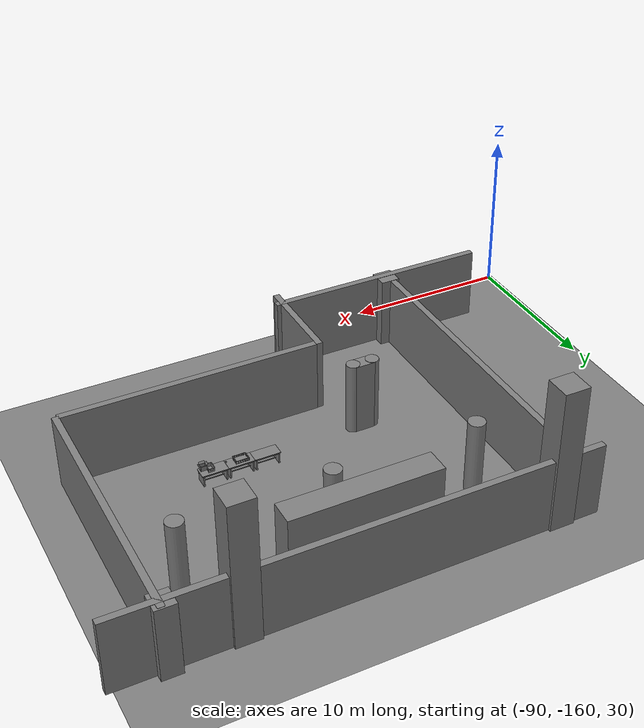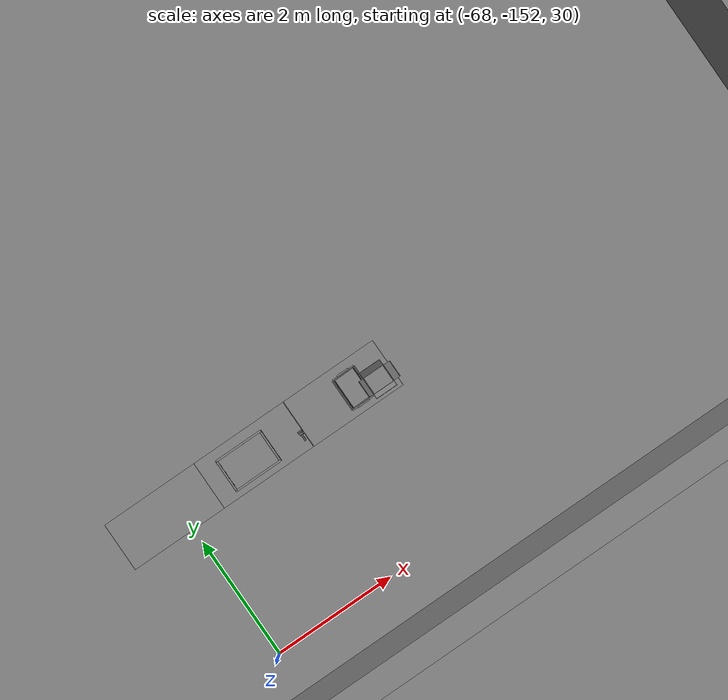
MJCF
<mujoco>
    <option gravity="0.000000000 0.000000000 -9.810000420" timestep="0.0049999999" integrator="implicitfast" density="1.225" viscosity="1.8000001e-05" noslip_iterations="10" iterations="100" sdf_iterations="50">
        <flag multiccd="disable"/>
    </option>
    <size memory="1000M"/>
    <compiler coordinate="local"/>
    <worldbody>
        <light cutoff="30" pos="0 1 1" dir="0 -1 -2"/>
        <light cutoff="30" pos="0 -1 1" dir="0 1 -2"/>
        <body pos="-64.866622925 -149.383972168 30.183746338" euler="89.999992371 89.999946594 0.000000000" name="openloong_gripper_2f85_fix_base_usda_bluebox_01">
            <geom contype="1" conaffinity="1" density="1000" type="box" material="" rgba="0.500000000 0.500000000 0.500000000 1.000000000" solimp="0.899999976 0.949999988 0.001000000" friction="1.000000000 0.005000000 0.000100000" solref="0.020000000 1.000000000" margin="0" condim="3" group="0" pos="0.276596069 0.187225342 0.000061035" quat="0.707107008 0.000077501 0.707106471 0.000077456" size="0.100000001 0.057999998 0.010000000" name="openloong_gripper_2f85_fix_base_usda_geom_6B4420B0_6584_440E_A277_6266138B9996"/>
            <geom contype="1" conaffinity="1" density="1000" type="box" material="" rgba="0.500000000 0.500000000 0.500000000 1.000000000" solimp="0.899999976 0.949999988 0.001000000" friction="1.000000000 0.005000000 0.000100000" solref="0.020000000 1.000000000" margin="0" condim="3" group="0" pos="0.000000000 0.002883911 0.000000000" quat="1.000000000 0.000000000 0.000000000 0.000000000" size="0.254000008 0.003000000 0.172000006" name="openloong_gripper_2f85_fix_base_usda_geom_FFF55D38_BDBF_418D_BF7A_738CE297088F"/>
            <geom contype="1" conaffinity="1" density="1000" type="box" material="" rgba="0.500000000 0.500000000 0.500000000 1.000000000" solimp="0.899999976 0.949999988 0.001000000" friction="1.000000000 0.005000000 0.000100000" solref="0.020000000 1.000000000" margin="0" condim="3" group="0" pos="0.000015259 0.124874115 0.173477173" quat="0.999796450 0.020176515 -0.000000015 0.000000030" size="0.259999990 0.119999997 0.007000000" name="openloong_gripper_2f85_fix_base_usda_geom_B25912B0_0883_4FFA_8C44_E2F9711D9464"/>
            <geom contype="1" conaffinity="1" density="1000" type="box" material="" rgba="0.500000000 0.500000000 0.500000000 1.000000000" solimp="0.899999976 0.949999988 0.001000000" friction="1.000000000 0.005000000 0.000100000" solref="0.020000000 1.000000000" margin="0" condim="3" group="0" pos="0.000015259 0.124874115 -0.173477173" quat="0.999796450 -0.020176545 -0.000000015 0.000000000" size="0.259999990 0.119999997 0.007000000" name="openloong_gripper_2f85_fix_base_usda_geom_D313A4A1_4156_455F_8F49_4D7EB0D48220"/>
            <geom contype="1" conaffinity="1" density="1000" type="box" material="" rgba="0.500000000 0.500000000 0.500000000 1.000000000" solimp="0.899999976 0.949999988 0.001000000" friction="1.000000000 0.005000000 0.000100000" solref="0.020000000 1.000000000" margin="0" condim="3" group="0" pos="0.000015259 0.214012146 0.188980103" quat="0.999913096 0.013176724 0.000000015 0.000000000" size="0.259999990 0.029999999 0.012500000" name="openloong_gripper_2f85_fix_base_usda_geom_08F78DDB_5AAB_4006_977E_DF1A623C7C15"/>
            <geom contype="1" conaffinity="1" density="1000" type="box" material="" rgba="0.500000000 0.500000000 0.500000000 1.000000000" solimp="0.899999976 0.949999988 0.001000000" friction="1.000000000 0.005000000 0.000100000" solref="0.020000000 1.000000000" margin="0" condim="3" group="0" pos="-0.258346558 0.125289917 0.001876831" quat="0.702796996 -0.020792052 0.710783184 0.020769238" size="0.189999998 0.119999997 0.009000000" name="openloong_gripper_2f85_fix_base_usda_geom_332EE5C4_CA2C_448F_BCAB_6F7270B4536B"/>
            <geom contype="1" conaffinity="1" density="1000" type="box" material="" rgba="0.500000000 0.500000000 0.500000000 1.000000000" solimp="0.899999976 0.949999988 0.001000000" friction="1.000000000 0.005000000 0.000100000" solref="0.020000000 1.000000000" margin="0" condim="3" group="0" pos="0.000015259 0.214012146 -0.188980103" quat="0.999913096 -0.013176769 0.000000030 0.000000015" size="0.259999990 0.029999999 0.012500000" name="openloong_gripper_2f85_fix_base_usda_geom_1ACCE175_5F62_4C7A_BB35_A32D66A985AD"/>
            <geom contype="1" conaffinity="1" density="1000" type="box" material="" rgba="0.500000000 0.500000000 0.500000000 1.000000000" solimp="0.899999976 0.949999988 0.001000000" friction="1.000000000 0.005000000 0.000100000" solref="0.020000000 1.000000000" margin="0" condim="3" group="0" pos="-0.276596069 0.187225342 0.000061035" quat="0.707106650 0.000077441 0.707106709 0.000077456" size="0.100000001 0.057999998 0.010000000" name="openloong_gripper_2f85_fix_base_usda_geom_1168961E_A1A4_4A5A_9C3B_CCD899C18095"/>
            <geom contype="1" conaffinity="1" density="1000" type="box" material="" rgba="0.500000000 0.500000000 0.500000000 1.000000000" solimp="0.899999976 0.949999988 0.001000000" friction="1.000000000 0.005000000 0.000100000" solref="0.020000000 1.000000000" margin="0" condim="3" group="0" pos="0.258346558 0.125289917 0.001876831" quat="0.702851534 0.018856451 0.710823834 -0.019329429" size="0.189999998 0.119999997 0.009000000" name="openloong_gripper_2f85_fix_base_usda_geom_505423D1_B2AF_456F_B6CD_465A68F512CA"/>
            <freejoint name="openloong_gripper_2f85_fix_base_usda_bluebox_01_joint"/>
            <site size="0.005000000 0.005000000 0.005000000" rgba="0.500000000 0.500000000 0.500000000 1.000000000" pos="0.000000000 0.000000000 0.000000000" quat="0.999961913 0.008726534 0.000000000 0.000000000" group="0" type="sphere" name="openloong_gripper_2f85_fix_base_usda_bluebox_01site"/>
        </body>
        <body pos="-64.496299744 -149.491867065 30.235729218" euler="0.000000000 0.000000000 89.999946594" name="openloong_gripper_2f85_fix_base_usda_cardboardbox_01">
            <geom contype="1" conaffinity="1" density="1000" type="box" material="" rgba="0.500000000 0.500000000 0.500000000 1.000000000" solimp="0.899999976 0.949999988 0.001000000" friction="1.000000000 0.005000000 0.000100000" solref="0.020000000 1.000000000" margin="0" condim="3" group="0" pos="-0.003166199 -0.004086494 0.005052090" quat="1.000000000 0.000000000 0.000000000 0.000000000" size="0.142499998 0.177500010 0.005000000" name="openloong_gripper_2f85_fix_base_usda_geom_D19706C4_184F_427A_8315_D43C8E9C0645"/>
            <geom contype="1" conaffinity="1" density="1000" type="box" material="" rgba="0.500000000 0.500000000 0.500000000 1.000000000" solimp="0.899999976 0.949999988 0.001000000" friction="1.000000000 0.005000000 0.000100000" solref="0.020000000 1.000000000" margin="0" condim="3" group="0" pos="-0.003166199 0.170316696 0.150570869" quat="1.000000000 0.000000000 0.000000000 0.000000000" size="0.142499998 0.005000000 0.149999991" name="openloong_gripper_2f85_fix_base_usda_geom_6F19C523_1D25_4BFB_8DC7_CA1DAF1FEA48"/>
            <geom contype="1" conaffinity="1" density="1000" type="box" material="" rgba="0.500000000 0.500000000 0.500000000 1.000000000" solimp="0.899999976 0.949999988 0.001000000" friction="1.000000000 0.005000000 0.000100000" solref="0.020000000 1.000000000" margin="0" condim="3" group="0" pos="-0.147399902 -0.005307198 0.150570869" quat="1.000000000 0.000000000 0.000000000 0.000000000" size="0.005000000 0.177500010 0.149999991" name="openloong_gripper_2f85_fix_base_usda_geom_5DC97697_A279_4835_8008_D9CF500793B0"/>
            <geom contype="1" conaffinity="1" density="1000" type="box" material="" rgba="0.500000000 0.500000000 0.500000000 1.000000000" solimp="0.899999976 0.949999988 0.001000000" friction="1.000000000 0.005000000 0.000100000" solref="0.020000000 1.000000000" margin="0" condim="3" group="0" pos="0.140275955 -0.005307198 0.150570869" quat="1.000000000 0.000000000 0.000000000 0.000000000" size="0.005000000 0.177500010 0.149999991" name="openloong_gripper_2f85_fix_base_usda_geom_06CD8075_ABF0_41FB_AC26_E2F99D8E57B4"/>
            <geom contype="1" conaffinity="1" density="1000" type="box" material="" rgba="0.500000000 0.500000000 0.500000000 1.000000000" solimp="0.899999976 0.949999988 0.001000000" friction="1.000000000 0.005000000 0.000100000" solref="0.020000000 1.000000000" margin="0" condim="3" group="0" pos="-0.003166199 -0.181550980 0.150570869" quat="1.000000000 0.000000000 0.000000000 0.000000000" size="0.142499998 0.005000000 0.149999991" name="openloong_gripper_2f85_fix_base_usda_geom_DC140FA2_3D46_443E_9FF5_FE55E4543C11"/>
            <freejoint name="openloong_gripper_2f85_fix_base_usda_cardboardbox_01_joint"/>
            <site size="0.005000000 0.005000000 0.005000000" rgba="0.500000000 0.500000000 0.500000000 1.000000000" pos="0.000000000 0.000000000 0.000000000" quat="0.999961913 0.008726535 0.000000000 0.000000000" group="0" type="sphere" name="openloong_gripper_2f85_fix_base_usda_site_B56A51B7_BC24_402C_8AD1_2496CBA7BBED"/>
            <body pos="0.139160156 -0.004048347 0.301930904" euler="-179.999954224 49.383502960 179.999954224" name="openloong_gripper_2f85_fix_base_usda_A1_006">
                <geom contype="1" conaffinity="1" density="1000" type="box" material="" rgba="0.500000000 0.500000000 0.500000000 1.000000000" solimp="0.899999976 0.949999988 0.001000000" friction="1.000000000 0.005000000 0.000100000" solref="0.020000000 1.000000000" margin="0" condim="3" group="0" pos="-0.071587563 0.000009537 0.001745224" quat="0.999999881 0.000000000 0.000000000 0.000000000" size="0.071249999 0.179999992 0.002500000" name="openloong_gripper_2f85_fix_base_usda_geom_15F0E053_5C82_4B75_ADC5_2A639BABFD6D"/>
                <joint armature="0" stiffness="0.07" damping="0.0099999998" axis="0.000000 1.000000 0.000000" type="hinge" name="openloong_gripper_2f85_fix_base_usda_A1_006"/>
            </body>
            <body pos="-0.145902634 -0.004086494 0.301938057" euler="-180.000000000 -60.000011444 -180.000000000" name="openloong_gripper_2f85_fix_base_usda_A2_006">
                <geom contype="1" conaffinity="1" density="1000" type="box" material="" rgba="0.500000000 0.500000000 0.500000000 1.000000000" solimp="0.899999976 0.949999988 0.001000000" friction="1.000000000 0.005000000 0.000100000" solref="0.020000000 1.000000000" margin="0" condim="3" group="0" pos="0.071268082 0.000009537 0.002717972" quat="0.000002921 0.000000000 -0.000000030 0.999999881" size="0.071249999 0.179999992 0.002500000" name="openloong_gripper_2f85_fix_base_usda_geom_9CC4CD4F_13FD_42DF_8884_E19BEC46F4D4"/>
                <joint armature="0" stiffness="0.07" damping="0.0099999998" axis="0.000000 1.000000 0.000000" type="hinge" name="openloong_gripper_2f85_fix_base_usda_A2_006"/>
            </body>
            <body pos="-0.003385544 0.175991058 0.301930904" euler="-125.858116150 -0.000004561 0.000002331" name="openloong_gripper_2f85_fix_base_usda_B2_006">
                <geom contype="1" conaffinity="1" density="1000" type="box" material="" rgba="0.500000000 0.500000000 0.500000000 1.000000000" solimp="0.899999976 0.949999988 0.001000000" friction="1.000000000 0.005000000 0.000100000" solref="0.020000000 1.000000000" margin="0" condim="3" group="0" pos="0.000009537 -0.070939064 -0.002470016" quat="0.999614120 0.027776197 -0.000000015 0.000000030" size="0.137500003 0.064999998 0.005000000" name="openloong_gripper_2f85_fix_base_usda_geom_12E49E91_2A7B_439B_90AA_72FD1653AED7"/>
                <joint armature="0" stiffness="0.07" damping="0.0099999998" axis="1.000000 0.000000 0.000000" type="hinge" name="openloong_gripper_2f85_fix_base_usda_B2_006"/>
            </body>
            <body pos="-0.003385544 -0.184140205 0.301938057" euler="147.805557251 0.000000000 0.000000000" name="openloong_gripper_2f85_fix_base_usda_B1_006">
                <geom contype="1" conaffinity="1" density="1000" type="box" material="" rgba="0.500000000 0.500000000 0.500000000 1.000000000" solimp="0.899999976 0.949999988 0.001000000" friction="1.000000000 0.005000000 0.000100000" solref="0.020000000 1.000000000" margin="0" condim="3" group="0" pos="-0.000028610 0.070202351 -0.002703667" quat="0.999614179 -0.027776167 0.000000000 0.000000000" size="0.137500003 0.064999998 0.005000000" name="openloong_gripper_2f85_fix_base_usda_geom_E1CEC3F8_F7D1_4A73_89CE_525CCCE745F4"/>
                <joint armature="0" stiffness="0.07" damping="0.0099999998" axis="1.000000 0.000000 0.000000" type="hinge" name="openloong_gripper_2f85_fix_base_usda_B1_006"/>
            </body>
        </body>
        <body pos="-65.882858276 -149.481979370 30.229999542" euler="-64.487716675 0.000000000 0.000000000" name="openloong_gripper_2f85_fix_base_usda_Barcode">
            <geom contype="1" conaffinity="1" density="1000" type="box" material="" rgba="0.500000000 0.500000000 0.500000000 1.000000000" solimp="0.899999976 0.949999988 0.001000000" friction="1.000000000 0.005000000 0.000100000" solref="0.020000000 1.000000000" margin="0" condim="3" group="0" pos="0.000000000 0.013038635 0.001419067" quat="0.000000000 0.000000000 0.000000000 1.000000119" size="0.034000002 0.010000000 0.017999999" name="openloong_gripper_2f85_fix_base_usda_geom_E2ED8F9D_FC3C_4E3F_960D_25BE8B3F98CB"/>
            <geom contype="1" conaffinity="1" density="1000" type="box" material="" rgba="0.500000000 0.500000000 0.500000000 1.000000000" solimp="0.899999976 0.949999988 0.001000000" friction="1.000000000 0.005000000 0.000100000" solref="0.020000000 1.000000000" margin="0" condim="3" group="0" pos="0.000000000 -0.035301208 -0.007095337" quat="0.000000000 0.000000000 -0.043619365 0.999048233" size="0.028999999 0.010000000 0.020000000" name="openloong_gripper_2f85_fix_base_usda_geom_EBE7A05C_96DB_417C_8A8F_1595DB49B7F2"/>
            <geom contype="1" conaffinity="1" density="1000" type="box" material="" rgba="0.500000000 0.500000000 0.500000000 1.000000000" solimp="0.899999976 0.949999988 0.001000000" friction="1.000000000 0.005000000 0.000100000" solref="0.020000000 1.000000000" margin="0" condim="3" group="0" pos="0.000000000 -0.043411255 -0.011749268" quat="0.922262907 0.386563420 0.000000000 0.000000000" size="0.026000001 0.010000000 0.020000000" name="openloong_gripper_2f85_fix_base_usda_geom_E8BADBD3_C6DD_4C1B_BF2D_8EB829B333FA"/>
            <geom contype="1" conaffinity="1" density="1000" type="box" material="" rgba="0.500000000 0.500000000 0.500000000 1.000000000" solimp="0.899999976 0.949999988 0.001000000" friction="1.000000000 0.005000000 0.000100000" solref="0.020000000 1.000000000" margin="0" condim="3" group="0" pos="0.000000000 -0.016967773 -0.031860352" quat="0.000000000 0.000000000 0.000000000 1.000000119" size="0.008000000 0.010000000 0.013000000" name="openloong_gripper_2f85_fix_base_usda_geom_BD886C12_E267_46A4_BFCF_3B94A101D1C5"/>
            <geom contype="1" conaffinity="1" density="1000" type="box" material="" rgba="0.500000000 0.500000000 0.500000000 1.000000000" solimp="0.899999976 0.949999988 0.001000000" friction="1.000000000 0.005000000 0.000100000" solref="0.020000000 1.000000000" margin="0" condim="3" group="0" pos="0.000000000 -0.001869202 0.000312805" quat="0.953716993 0.300705761 0.000000000 0.000000000" size="0.032000002 0.010000000 0.018999999" name="openloong_gripper_2f85_fix_base_usda_geom_1D67DA60_D113_460F_8623_96FC54203303"/>
            <geom contype="1" conaffinity="1" density="1000" type="box" material="" rgba="0.500000000 0.500000000 0.500000000 1.000000000" solimp="0.899999976 0.949999988 0.001000000" friction="1.000000000 0.005000000 0.000100000" solref="0.020000000 1.000000000" margin="0" condim="3" group="0" pos="0.000000000 -0.019531250 -0.003173828" quat="0.953716993 0.300705761 0.000000000 0.000000000" size="0.030999999 0.010000000 0.020000000" name="openloong_gripper_2f85_fix_base_usda_geom_E0BEDAC2_16F3_4ED0_ACF4_7F297A0AFEE6"/>
            <geom contype="1" conaffinity="1" density="1000" type="box" material="" rgba="0.500000000 0.500000000 0.500000000 1.000000000" solimp="0.899999976 0.949999988 0.001000000" friction="1.000000000 0.005000000 0.000100000" solref="0.020000000 1.000000000" margin="0" condim="3" group="0" pos="0.000000000 -0.035301208 -0.007095337" quat="0.953716993 0.300705761 0.000000000 0.000000000" size="0.028999999 0.010000000 0.020000000" name="openloong_gripper_2f85_fix_base_usda_geom_3B7C654D_78F5_4472_A9D1_2DD141318188"/>
            <geom contype="1" conaffinity="1" density="1000" type="box" material="" rgba="0.500000000 0.500000000 0.500000000 1.000000000" solimp="0.899999976 0.949999988 0.001000000" friction="1.000000000 0.005000000 0.000100000" solref="0.020000000 1.000000000" margin="0" condim="3" group="0" pos="0.000000000 -0.042617798 -0.071121216" quat="0.000000000 0.000000000 0.000000000 1.000000119" size="0.013000000 0.021000000 0.059999999" name="openloong_gripper_2f85_fix_base_usda_geom_ADF333E5_5814_4988_86BD_5CBB777C6FEF"/>
            <freejoint name="openloong_gripper_2f85_fix_base_usda_Barcode_joint"/>
            <site size="0.005000000 0.005000000 0.005000000" rgba="0.500000000 0.500000000 0.500000000 1.000000000" pos="0.000000000 0.000000000 0.000000000" quat="1.000000000 0.000000000 0.000000000 0.000000000" group="0" type="sphere" name="openloong_gripper_2f85_fix_base_usda_Barcode_site"/>
        </body>
        <body pos="-66.745018005 -149.392349243 30.184000015" euler="0.000000000 0.000000000 89.999946594" name="[22333710063039]_Basket_01">
            <geom contype="1" conaffinity="1" density="1000" type="box" material="" rgba="0.500000000 0.500000000 0.500000000 1.000000000" solimp="0.899999976 0.949999988 0.001000000" friction="1.000000000 0.005000000 0.000100000" solref="0.020000000 1.000000000" margin="0" condim="3" group="0" pos="-0.052425385 0.389207840 0.089787483" quat="0.707107008 0.000000000 0.000000000 0.707106411" size="0.014249999 0.014249999 0.059999999" name="[22333710063039]_geom_C5A743E5_7C54_4598_AAD7_D1D01A5CE8C1"/>
            <geom contype="1" conaffinity="1" density="1000" type="box" material="" rgba="0.500000000 0.500000000 0.500000000 1.000000000" solimp="0.899999976 0.949999988 0.001000000" friction="1.000000000 0.005000000 0.000100000" solref="0.020000000 1.000000000" margin="0" condim="3" group="0" pos="0.264015198 -0.133043289 0.089787483" quat="0.707107008 0.000000000 0.000000000 0.707106411" size="0.014249999 0.014249999 0.059999999" name="[22333710063039]_geom_491B2C2A_D9C3_48B1_8CC8_6A1F068CCA98"/>
            <geom contype="1" conaffinity="1" density="1000" type="box" material="" rgba="0.500000000 0.500000000 0.500000000 1.000000000" solimp="0.899999976 0.949999988 0.001000000" friction="1.000000000 0.005000000 0.000100000" solref="0.020000000 1.000000000" margin="0" condim="3" group="0" pos="-0.264015198 -0.265548706 0.089793205" quat="0.707107008 0.000000000 0.000000000 0.707106411" size="0.014249999 0.014249999 0.059999999" name="[22333710063039]_geom_60D0536E_EF99_4F35_A675_33D083CC5767"/>
            <geom contype="1" conaffinity="1" density="1000" type="box" material="" rgba="0.500000000 0.500000000 0.500000000 1.000000000" solimp="0.899999976 0.949999988 0.001000000" friction="1.000000000 0.005000000 0.000100000" solref="0.020000000 1.000000000" margin="0" condim="3" group="0" pos="-0.160263062 -0.389322281 0.089793205" quat="0.707107008 0.000000000 0.000000000 0.707106411" size="0.014249999 0.014249999 0.059999999" name="[22333710063039]_geom_B6F8C63C_9D03_41A6_BBA3_FB81E2404386"/>
            <geom contype="1" conaffinity="1" density="1000" type="box" material="" rgba="0.500000000 0.500000000 0.500000000 1.000000000" solimp="0.899999976 0.949999988 0.001000000" friction="1.000000000 0.005000000 0.000100000" solref="0.020000000 1.000000000" margin="0" condim="3" group="0" pos="0.162265778 -0.389322281 0.089787483" quat="0.707107008 0.000000000 0.000000000 0.707106411" size="0.014249999 0.014249999 0.059999999" name="[22333710063039]_geom_5D87FB4C_165D_4042_B4C2_F6625C0E9F83"/>
            <geom contype="1" conaffinity="1" density="1000" type="box" material="" rgba="0.500000000 0.500000000 0.500000000 1.000000000" solimp="0.899999976 0.949999988 0.001000000" friction="1.000000000 0.005000000 0.000100000" solref="0.020000000 1.000000000" margin="0" condim="3" group="0" pos="0.264015198 0.389207840 0.089787483" quat="0.707107008 0.000000000 0.000000000 0.707106411" size="0.014249999 0.014249999 0.059999999" name="[22333710063039]_geom_80FCA0FB_C669_4632_A6AB_220F9D1E641A"/>
            <geom contype="1" conaffinity="1" density="1000" type="box" material="" rgba="0.500000000 0.500000000 0.500000000 1.000000000" solimp="0.899999976 0.949999988 0.001000000" friction="1.000000000 0.005000000 0.000100000" solref="0.020000000 1.000000000" margin="0" condim="3" group="0" pos="-0.264015198 -0.133043289 0.089793205" quat="0.707107008 0.000000000 0.000000000 0.707106411" size="0.014249999 0.014249999 0.059999999" name="[22333710063039]_geom_2DC62912_DA91_4C1B_8665_E28358EAD2E0"/>
            <geom contype="1" conaffinity="1" density="1000" type="box" material="" rgba="0.500000000 0.500000000 0.500000000 1.000000000" solimp="0.899999976 0.949999988 0.001000000" friction="1.000000000 0.005000000 0.000100000" solref="0.020000000 1.000000000" margin="0" condim="3" group="0" pos="-0.264026642 0.269256592 0.089793205" quat="0.707107008 0.000000000 0.000000000 0.707106411" size="0.014249999 0.014249999 0.059999999" name="[22333710063039]_geom_984CB0FF_C668_4475_992D_530F0E59E4E1"/>
            <geom contype="1" conaffinity="1" density="1000" type="box" material="" rgba="0.500000000 0.500000000 0.500000000 1.000000000" solimp="0.899999976 0.949999988 0.001000000" friction="1.000000000 0.005000000 0.000100000" solref="0.020000000 1.000000000" margin="0" condim="3" group="0" pos="0.054462433 0.389207840 0.089787483" quat="0.707107008 0.000000000 0.000000000 0.707106411" size="0.014249999 0.014249999 0.059999999" name="[22333710063039]_geom_A2584D29_854D_4742_BA13_B572368F0E8A"/>
            <geom contype="1" conaffinity="1" density="1000" type="box" material="" rgba="0.500000000 0.500000000 0.500000000 1.000000000" solimp="0.899999976 0.949999988 0.001000000" friction="1.000000000 0.005000000 0.000100000" solref="0.020000000 1.000000000" margin="0" condim="3" group="0" pos="0.054462433 -0.389322281 0.089787483" quat="0.707107008 0.000000000 0.000000000 0.707106411" size="0.014249999 0.014249999 0.059999999" name="[22333710063039]_geom_24C20649_D322_4BC9_B8A6_84818D930BF4"/>
            <geom contype="1" conaffinity="1" density="1000" type="box" material="" rgba="0.500000000 0.500000000 0.500000000 1.000000000" solimp="0.899999976 0.949999988 0.001000000" friction="1.000000000 0.005000000 0.000100000" solref="0.020000000 1.000000000" margin="0" condim="3" group="0" pos="0.264015198 0.269256592 0.089793205" quat="0.707107008 0.000000000 0.000000000 0.707106411" size="0.014249999 0.014249999 0.059999999" name="[22333710063039]_geom_FCA94033_0123_4C68_BFAE_C5F527E19929"/>
            <geom contype="1" conaffinity="1" density="1000" type="box" material="" rgba="0.500000000 0.500000000 0.500000000 1.000000000" solimp="0.899999976 0.949999988 0.001000000" friction="1.000000000 0.005000000 0.000100000" solref="0.020000000 1.000000000" margin="0" condim="3" group="0" pos="0.264015198 -0.389322281 0.089787483" quat="0.707107008 0.000000000 0.000000000 0.707106411" size="0.014249999 0.014249999 0.059999999" name="[22333710063039]_geom_FBE58AC5_1969_4369_93C8_9FB0E1E0DBFC"/>
            <geom contype="1" conaffinity="1" density="1000" type="box" material="" rgba="0.500000000 0.500000000 0.500000000 1.000000000" solimp="0.899999976 0.949999988 0.001000000" friction="1.000000000 0.005000000 0.000100000" solref="0.020000000 1.000000000" margin="0" condim="3" group="0" pos="0.000000000 0.000000000 0.015998840" quat="0.707107008 0.000000000 0.000000000 0.707106411" size="0.403499991 0.279000014 0.015750000" name="[22333710063039]_geom_B881863D_7D75_419F_A7DC_A183E82A4CF9"/>
            <geom contype="1" conaffinity="1" density="1000" type="box" material="" rgba="0.500000000 0.500000000 0.500000000 1.000000000" solimp="0.899999976 0.949999988 0.001000000" friction="1.000000000 0.005000000 0.000100000" solref="0.020000000 1.000000000" margin="0" condim="3" group="0" pos="0.000000000 -0.389476776 0.163619041" quat="0.707107008 0.000000000 0.000000000 0.707106411" size="0.015000000 0.277500004 0.015750000" name="[22333710063039]_geom_78093A04_10E0_4F23_9143_8E9A0FEF715A"/>
            <geom contype="1" conaffinity="1" density="1000" type="box" material="" rgba="0.500000000 0.500000000 0.500000000 1.000000000" solimp="0.899999976 0.949999988 0.001000000" friction="1.000000000 0.005000000 0.000100000" solref="0.020000000 1.000000000" margin="0" condim="3" group="0" pos="0.162265778 0.389207840 0.089787483" quat="0.707107008 0.000000000 0.000000000 0.707106411" size="0.014249999 0.014249999 0.059999999" name="[22333710063039]_geom_AFE5D0BA_1015_42BA_8904_992816B6847F"/>
            <geom contype="1" conaffinity="1" density="1000" type="box" material="" rgba="0.500000000 0.500000000 0.500000000 1.000000000" solimp="0.899999976 0.949999988 0.001000000" friction="1.000000000 0.005000000 0.000100000" solref="0.020000000 1.000000000" margin="0" condim="3" group="0" pos="0.000000000 0.389471054 0.163619041" quat="0.707107008 0.000000000 0.000000000 0.707106411" size="0.015000000 0.277500004 0.015750000" name="[22333710063039]_geom_C7290222_1B35_4FCA_AC6C_52A4783D08E8"/>
            <geom contype="1" conaffinity="1" density="1000" type="box" material="" rgba="0.500000000 0.500000000 0.500000000 1.000000000" solimp="0.899999976 0.949999988 0.001000000" friction="1.000000000 0.005000000 0.000100000" solref="0.020000000 1.000000000" margin="0" condim="3" group="0" pos="-0.263511658 0.000000000 0.163619041" quat="0.707107008 0.000000000 0.000000000 0.707106411" size="0.403499991 0.015000000 0.015750000" name="[22333710063039]_geom_C2D4C3C7_24D9_4CB9_AB57_62FA40AE13C5"/>
            <geom contype="1" conaffinity="1" density="1000" type="box" material="" rgba="0.500000000 0.500000000 0.500000000 1.000000000" solimp="0.899999976 0.949999988 0.001000000" friction="1.000000000 0.005000000 0.000100000" solref="0.020000000 1.000000000" margin="0" condim="3" group="0" pos="-0.264015198 0.141334534 0.089793205" quat="0.707107008 0.000000000 0.000000000 0.707106411" size="0.014249999 0.014249999 0.059999999" name="[22333710063039]_geom_83385018_B31C_4A0D_AED9_C99B5C6A6AA0"/>
            <geom contype="1" conaffinity="1" density="1000" type="box" material="" rgba="0.500000000 0.500000000 0.500000000 1.000000000" solimp="0.899999976 0.949999988 0.001000000" friction="1.000000000 0.005000000 0.000100000" solref="0.020000000 1.000000000" margin="0" condim="3" group="0" pos="0.264015198 -0.265548706 0.089787483" quat="0.707107008 0.000000000 0.000000000 0.707106411" size="0.014249999 0.014249999 0.059999999" name="[22333710063039]_geom_F9A1918B_79DE_4B46_A4A3_7296A5A214F6"/>
            <geom contype="1" conaffinity="1" density="1000" type="box" material="" rgba="0.500000000 0.500000000 0.500000000 1.000000000" solimp="0.899999976 0.949999988 0.001000000" friction="1.000000000 0.005000000 0.000100000" solref="0.020000000 1.000000000" margin="0" condim="3" group="0" pos="-0.160263062 0.389207840 0.089787483" quat="0.707107008 0.000000000 0.000000000 0.707106411" size="0.014249999 0.014249999 0.059999999" name="[22333710063039]_geom_527C1CB8_0E37_46A8_9848_350A8DB9E44B"/>
            <geom contype="1" conaffinity="1" density="1000" type="box" material="" rgba="0.500000000 0.500000000 0.500000000 1.000000000" solimp="0.899999976 0.949999988 0.001000000" friction="1.000000000 0.005000000 0.000100000" solref="0.020000000 1.000000000" margin="0" condim="3" group="0" pos="-0.052425385 -0.389322281 0.089787483" quat="0.707107008 0.000000000 0.000000000 0.707106411" size="0.014249999 0.014249999 0.059999999" name="[22333710063039]_geom_BD7AFF96_FC5B_4476_8CA5_5CB4C0FAD11D"/>
            <geom contype="1" conaffinity="1" density="1000" type="box" material="" rgba="0.500000000 0.500000000 0.500000000 1.000000000" solimp="0.899999976 0.949999988 0.001000000" friction="1.000000000 0.005000000 0.000100000" solref="0.020000000 1.000000000" margin="0" condim="3" group="0" pos="-0.264026642 -0.389322281 0.089793205" quat="0.707107008 0.000000000 0.000000000 0.707106411" size="0.014249999 0.014249999 0.059999999" name="[22333710063039]_geom_C8344B86_C53A_44D2_A2BF_1ECA692FBBD8"/>
            <geom contype="1" conaffinity="1" density="1000" type="box" material="" rgba="0.500000000 0.500000000 0.500000000 1.000000000" solimp="0.899999976 0.949999988 0.001000000" friction="1.000000000 0.005000000 0.000100000" solref="0.020000000 1.000000000" margin="0" condim="3" group="0" pos="0.264015198 0.141334534 0.089787483" quat="0.707107008 0.000000000 0.000000000 0.707106411" size="0.014249999 0.014249999 0.059999999" name="[22333710063039]_geom_30B00CA6_60FA_4050_9311_00E76EB42552"/>
            <geom contype="1" conaffinity="1" density="1000" type="box" material="" rgba="0.500000000 0.500000000 0.500000000 1.000000000" solimp="0.899999976 0.949999988 0.001000000" friction="1.000000000 0.005000000 0.000100000" solref="0.020000000 1.000000000" margin="0" condim="3" group="0" pos="-0.264015198 0.389207840 0.089793205" quat="0.707107008 0.000000000 0.000000000 0.707106411" size="0.014249999 0.014249999 0.059999999" name="[22333710063039]_geom_1D33E9A2_04FA_45A6_B369_299A1B3582F4"/>
            <geom contype="1" conaffinity="1" density="1000" type="box" material="" rgba="0.500000000 0.500000000 0.500000000 1.000000000" solimp="0.899999976 0.949999988 0.001000000" friction="1.000000000 0.005000000 0.000100000" solref="0.020000000 1.000000000" margin="0" condim="3" group="0" pos="0.264015198 0.004480362 0.089787483" quat="0.707107008 0.000000000 0.000000000 0.707106411" size="0.014249999 0.014249999 0.059999999" name="[22333710063039]_geom_0B195577_CAF9_4F01_9B55_A15A754A7180"/>
            <geom contype="1" conaffinity="1" density="1000" type="box" material="" rgba="0.500000000 0.500000000 0.500000000 1.000000000" solimp="0.899999976 0.949999988 0.001000000" friction="1.000000000 0.005000000 0.000100000" solref="0.020000000 1.000000000" margin="0" condim="3" group="0" pos="0.263694763 -0.000011444 0.163619041" quat="0.707107008 0.000000000 0.000000000 0.707106411" size="0.403499991 0.015000000 0.015750000" name="[22333710063039]_geom_B814EBC3_D053_4C17_81CB_B8D4F1204D85"/>
            <geom contype="1" conaffinity="1" density="1000" type="box" material="" rgba="0.500000000 0.500000000 0.500000000 1.000000000" solimp="0.899999976 0.949999988 0.001000000" friction="1.000000000 0.005000000 0.000100000" solref="0.020000000 1.000000000" margin="0" condim="3" group="0" pos="-0.264015198 0.004480362 0.089793205" quat="0.707107008 0.000000000 0.000000000 0.707106411" size="0.014249999 0.014249999 0.059999999" name="[22333710063039]_geom_579B62F6_34D7_4A86_86E1_36E6148CD331"/>
            <freejoint name="[22333710063039]_joint_746ABBEA_B6F3_43E5_A727_C081DD844206"/>
        </body>
        <body pos="0.000000000 0.000000000 0.000000000" euler="0.000000000 0.000000000 0.000000000" name="Static Objects_Static Objects">
            <geom contype="1" conaffinity="1" density="1000" type="box" material="" rgba="0.500000000 0.500000000 0.500000000 1.000000000" solimp="0.899999976 0.949999988 0.001000000" friction="1.000000000 0.005000000 0.000100000" solref="0.020000000 1.000000000" margin="0" condim="3" group="0" pos="-67.544113159 -149.365814209 29.727830887" quat="0.500000417 0.499999970 0.499999553 0.499999970" size="0.381000012 0.319999993 0.041000001" name="Static Objects_geom_139D72D5_DA32_4AAD_8D37_A26D4271CC2B"/>
            <geom contype="1" conaffinity="1" density="1000" type="box" material="" rgba="0.500000000 0.500000000 0.500000000 1.000000000" solimp="0.899999976 0.949999988 0.001000000" friction="1.000000000 0.005000000 0.000100000" solref="0.020000000 1.000000000" margin="0" condim="3" group="0" pos="-68.239501953 -149.365814209 30.086868286" quat="0.500000417 0.499999970 0.499999553 0.499999970" size="0.370999992 0.039500002 0.745000005" name="Static Objects_geom_386D83FD_9307_4746_A6F3_7D9BE4410AE1"/>
            <geom contype="1" conaffinity="1" density="1000" type="box" material="" rgba="0.500000000 0.500000000 0.500000000 1.000000000" solimp="0.899999976 0.949999988 0.001000000" friction="1.000000000 0.005000000 0.000100000" solref="0.020000000 1.000000000" margin="0" condim="3" group="0" pos="-68.239501953 -149.365814209 30.147235870" quat="0.500000417 0.499999970 0.499999553 0.499999970" size="0.400000006 0.022000000 0.800000012" name="Static Objects_geom_E4ECC531_5B3F_4A4B_AD96_544E53933C5C"/>
            <geom contype="1" conaffinity="1" density="1000" type="box" material="" rgba="0.500000000 0.500000000 0.500000000 1.000000000" solimp="0.899999976 0.949999988 0.001000000" friction="1.000000000 0.005000000 0.000100000" solref="0.020000000 1.000000000" margin="0" condim="3" group="0" pos="-68.934890747 -149.365814209 29.727830887" quat="0.500000417 0.499999970 0.499999553 0.499999970" size="0.381000012 0.319999993 0.041000001" name="Static Objects_geom_28C61D46_5D5B_4D14_817C_0111B8C3A3AC"/>
            <geom contype="1" conaffinity="1" density="1000" type="box" material="" rgba="0.500000000 0.500000000 0.500000000 1.000000000" solimp="0.899999976 0.949999988 0.001000000" friction="1.000000000 0.005000000 0.000100000" solref="0.020000000 1.000000000" margin="0" condim="3" group="0" pos="-68.239501953 -149.365814209 29.561563492" quat="0.500000417 0.499999970 0.499999553 0.499999970" size="0.020000000 0.022000000 0.660000026" name="Static Objects_geom_60E58F72_6262_418E_ACC8_DB175721F1F2"/>
            <geom contype="1" conaffinity="1" density="1000" type="box" material="" rgba="0.500000000 0.500000000 0.500000000 1.000000000" solimp="0.899999976 0.949999988 0.001000000" friction="1.000000000 0.005000000 0.000100000" solref="0.020000000 1.000000000" margin="0" condim="3" group="0" pos="-65.945671082 -149.365814209 29.727830887" quat="0.500000417 0.499999970 0.499999553 0.499999970" size="0.381000012 0.319999993 0.041000001" name="Static Objects_geom_268BA166_0466_4C36_9FFF_147E768BA418"/>
            <geom contype="1" conaffinity="1" density="1000" type="box" material="" rgba="0.500000000 0.500000000 0.500000000 1.000000000" solimp="0.899999976 0.949999988 0.001000000" friction="1.000000000 0.005000000 0.000100000" solref="0.020000000 1.000000000" margin="0" condim="3" group="0" pos="-66.641059875 -149.365814209 30.086868286" quat="0.500000417 0.499999970 0.499999553 0.499999970" size="0.370999992 0.039500002 0.745000005" name="Static Objects_geom_C545F6D0_4A9A_4CC3_91F5_DAE7F608DB4D"/>
            <geom contype="1" conaffinity="1" density="1000" type="box" material="" rgba="0.500000000 0.500000000 0.500000000 1.000000000" solimp="0.899999976 0.949999988 0.001000000" friction="1.000000000 0.005000000 0.000100000" solref="0.020000000 1.000000000" margin="0" condim="3" group="0" pos="-66.641059875 -149.365814209 30.147235870" quat="0.500000417 0.499999970 0.499999553 0.499999970" size="0.400000006 0.022000000 0.800000012" name="Static Objects_geom_4357FB16_810F_4F5A_A552_FF4D68C8D20B"/>
            <geom contype="1" conaffinity="1" density="1000" type="box" material="" rgba="0.500000000 0.500000000 0.500000000 1.000000000" solimp="0.899999976 0.949999988 0.001000000" friction="1.000000000 0.005000000 0.000100000" solref="0.020000000 1.000000000" margin="0" condim="3" group="0" pos="-67.336448669 -149.365814209 29.727830887" quat="0.500000417 0.499999970 0.499999553 0.499999970" size="0.381000012 0.319999993 0.041000001" name="Static Objects_geom_B29652D7_E353_4D2C_8AEA_1372498DCE7C"/>
            <geom contype="1" conaffinity="1" density="1000" type="box" material="" rgba="0.500000000 0.500000000 0.500000000 1.000000000" solimp="0.899999976 0.949999988 0.001000000" friction="1.000000000 0.005000000 0.000100000" solref="0.020000000 1.000000000" margin="0" condim="3" group="0" pos="-66.641059875 -149.365814209 29.561563492" quat="0.500000417 0.499999970 0.499999553 0.499999970" size="0.020000000 0.022000000 0.660000026" name="Static Objects_geom_58BD4713_EC95_4B94_9AFC_7E83D8E81EAF"/>
            <geom contype="1" conaffinity="1" density="1000" type="box" material="" rgba="0.500000000 0.500000000 0.500000000 1.000000000" solimp="0.899999976 0.949999988 0.001000000" friction="1.000000000 0.005000000 0.000100000" solref="0.020000000 1.000000000" margin="0" condim="3" group="0" pos="-64.338577271 -149.365814209 29.727830887" quat="0.500000417 0.499999970 0.499999553 0.499999970" size="0.381000012 0.319999993 0.041000001" name="Static Objects_geom_04E4AEB6_C414_4044_BFFD_07DA1260D002"/>
            <geom contype="1" conaffinity="1" density="1000" type="box" material="" rgba="0.500000000 0.500000000 0.500000000 1.000000000" solimp="0.899999976 0.949999988 0.001000000" friction="1.000000000 0.005000000 0.000100000" solref="0.020000000 1.000000000" margin="0" condim="3" group="0" pos="-65.033966064 -149.365814209 30.086868286" quat="0.500000417 0.499999970 0.499999553 0.499999970" size="0.370999992 0.039500002 0.745000005" name="Static Objects_geom_A9A053C8_05C1_488D_B32E_BDC08C5440A2"/>
            <geom contype="1" conaffinity="1" density="1000" type="box" material="" rgba="0.500000000 0.500000000 0.500000000 1.000000000" solimp="0.899999976 0.949999988 0.001000000" friction="1.000000000 0.005000000 0.000100000" solref="0.020000000 1.000000000" margin="0" condim="3" group="0" pos="-65.033966064 -149.365814209 30.147235870" quat="0.500000417 0.499999970 0.499999553 0.499999970" size="0.400000006 0.022000000 0.800000012" name="Static Objects_geom_9BE6E8DF_CEBB_4D47_AC77_6C84EA29861C"/>
            <geom contype="1" conaffinity="1" density="1000" type="box" material="" rgba="0.500000000 0.500000000 0.500000000 1.000000000" solimp="0.899999976 0.949999988 0.001000000" friction="1.000000000 0.005000000 0.000100000" solref="0.020000000 1.000000000" margin="0" condim="3" group="0" pos="-65.729354858 -149.365814209 29.727830887" quat="0.500000417 0.499999970 0.499999553 0.499999970" size="0.381000012 0.319999993 0.041000001" name="Static Objects_geom_0906F098_543B_49EC_B082_01A24D35AD8D"/>
            <geom contype="1" conaffinity="1" density="1000" type="box" material="" rgba="0.500000000 0.500000000 0.500000000 1.000000000" solimp="0.899999976 0.949999988 0.001000000" friction="1.000000000 0.005000000 0.000100000" solref="0.020000000 1.000000000" margin="0" condim="3" group="0" pos="-65.033966064 -149.365814209 29.561563492" quat="0.500000417 0.499999970 0.499999553 0.499999970" size="0.020000000 0.022000000 0.660000026" name="Static Objects_geom_35196471_AFC9_4D63_AEAF_EB152B97F139"/>
            <geom contype="1" conaffinity="1" density="1000" type="box" material="" rgba="0.500000000 0.500000000 0.500000000 1.000000000" solimp="0.899999976 0.949999988 0.001000000" friction="1.000000000 0.005000000 0.000100000" solref="0.020000000 1.000000000" margin="0" condim="3" group="0" pos="-61.754566193 -137.853729248 33.906845093" quat="0.707107067 0.000000000 0.000000000 0.707106471" size="0.759999990 0.759999990 4.500000000" name="Static Objects_geom_3E77338E_A20C_49D0_A425_99A28C78CF38"/>
            <geom contype="1" conaffinity="1" density="1000" type="box" material="" rgba="0.500000000 0.500000000 0.500000000 1.000000000" solimp="0.899999976 0.949999988 0.001000000" friction="1.000000000 0.005000000 0.000100000" solref="0.020000000 1.000000000" margin="0" condim="3" group="0" pos="-57.511135101 -144.927108765 31.707921982" quat="1.000000000 0.000000000 0.000000000 0.000000000" size="0.200000003 8.000000000 2.299999952" name="Static Objects_geom_561206E0_3372_4258_BFF5_571B6166F4C2"/>
            <geom contype="1" conaffinity="1" density="1000" type="box" material="" rgba="0.500000000 0.500000000 0.500000000 1.000000000" solimp="0.899999976 0.949999988 0.001000000" friction="1.000000000 0.005000000 0.000100000" solref="0.020000000 1.000000000" margin="0" condim="3" group="0" pos="-80.517646790 -157.574050903 31.688196182" quat="0.707107067 0.000000000 0.000000000 0.707106471" size="0.600000024 0.600000024 2.299999952" name="Static Objects_geom_DDD64E60_84C3_4550_A3AA_30ECE61CFB1F"/>
            <geom contype="1" conaffinity="1" density="1000" type="box" material="" rgba="0.500000000 0.500000000 0.500000000 1.000000000" solimp="0.899999976 0.949999988 0.001000000" friction="1.000000000 0.005000000 0.000100000" solref="0.020000000 1.000000000" margin="0" condim="3" group="0" pos="-80.711044312 -147.414932251 31.666158676" quat="1.000000000 0.000000000 0.000000000 0.000000000" size="0.200000003 10.000000000 2.299999952" name="Static Objects_geom_43DDF41E_737B_4E20_89CD_03DF8CC77BAC"/>
            <geom contype="1" conaffinity="1" density="1000" type="box" material="" rgba="0.500000000 0.500000000 0.500000000 1.000000000" solimp="0.899999976 0.949999988 0.001000000" friction="1.000000000 0.005000000 0.000100000" solref="0.020000000 1.000000000" margin="0" condim="3" group="0" pos="-57.687217712 -137.434692383 31.688196182" quat="0.707107067 0.000000000 0.000000000 0.707106471" size="0.600000024 0.600000024 2.299999952" name="Static Objects_geom_671E049E_7BDF_47C0_A196_F6EF41FF7B93"/>
            <geom contype="1" conaffinity="1" density="1000" type="box" material="" rgba="0.500000000 0.500000000 0.500000000 1.000000000" solimp="0.899999976 0.949999988 0.001000000" friction="1.000000000 0.005000000 0.000100000" solref="0.020000000 1.000000000" margin="0" condim="3" group="0" pos="-69.537033081 -140.263229370 31.714921951" quat="0.707107067 0.000000000 0.000000000 0.707106471" size="0.759999990 4.500000000 2.299999952" name="Static Objects_geom_5B71AA23_B501_4E09_9F05_633FB681CA2B"/>
            <geom contype="1" conaffinity="1" density="1000" type="box" material="" rgba="0.500000000 0.500000000 0.500000000 1.000000000" solimp="0.899999976 0.949999988 0.001000000" friction="1.000000000 0.005000000 0.000100000" solref="0.020000000 1.000000000" margin="0" condim="3" group="0" pos="-80.073638916 -137.853713989 33.906845093" quat="0.707107067 0.000000000 0.000000000 0.707106471" size="0.759999990 0.759999990 4.500000000" name="Static Objects_geom_442D4F96_205D_47BE_B764_32BE8D8B368E"/>
            <geom contype="1" conaffinity="1" density="1000" type="box" material="" rgba="0.500000000 0.500000000 0.500000000 1.000000000" solimp="0.899999976 0.949999988 0.001000000" friction="1.000000000 0.005000000 0.000100000" solref="0.020000000 1.000000000" margin="0" condim="3" group="0" pos="-73.406707764 -155.734664917 31.707921982" quat="1.000000000 0.000000000 0.000000000 0.000000000" size="0.200000003 3.000000000 2.299999952" name="Static Objects_geom_4EE72D33_CE93_42CA_8020_9E87BCCB2B59"/>
            <geom contype="1" conaffinity="1" density="1000" type="box" material="" rgba="0.500000000 0.500000000 0.500000000 1.000000000" solimp="0.899999976 0.949999988 0.001000000" friction="1.000000000 0.005000000 0.000100000" solref="0.020000000 1.000000000" margin="0" condim="3" group="0" pos="-68.497543335 -137.448257446 31.707921982" quat="0.707107067 0.000000000 0.000000000 0.707106471" size="0.200000003 14.000000000 2.299999952" name="Static Objects_geom_69CF8A77_9B33_409B_B16A_0CEBECDB0913"/>
            <geom contype="1" conaffinity="1" density="1000" type="cylinder" material="" rgba="0.500000000 0.500000000 0.500000000 1.000000000" solimp="0.899999976 0.949999988 0.001000000" friction="1.000000000 0.005000000 0.000100000" solref="0.020000000 1.000000000" margin="0" condim="3" group="0" pos="-68.868522644 -142.134506226 31.711090088" quat="0.707107067 0.000000000 0.000000000 0.707106471" size="0.509999990 2.299999952 1.000000000" name="Static Objects_geom_E27917EE_9C3A_48B7_9FC2_52966B3D001F"/>
            <geom contype="1" conaffinity="1" density="1000" type="plane" material="" rgba="0.500000000 0.500000000 0.500000000 1.000000000" solimp="0.899999976 0.949999988 0.001000000" friction="1.000000000 0.005000000 0.000100000" solref="0.020000000 1.000000000" margin="0" condim="3" group="0" pos="-72.873703003 -147.131927490 29.409669876" quat="1.000000000 0.000000000 0.000000000 0.000000000" size="18.000000000 14.000000000 1.000000000" name="Static Objects_geom_18CAA7AD_622D_47A4_B1B7_4B978A1EA1B0"/>
            <geom contype="1" conaffinity="1" density="1000" type="box" material="" rgba="0.500000000 0.500000000 0.500000000 1.000000000" solimp="0.899999976 0.949999988 0.001000000" friction="1.000000000 0.005000000 0.000100000" solref="0.020000000 1.000000000" margin="0" condim="3" group="0" pos="-79.943580627 -157.782272339 31.707921982" quat="0.707107067 0.000000000 0.000000000 0.707106471" size="0.200000003 7.000000000 2.299999952" name="Static Objects_geom_5C7EF8D3_81AE_4EC7_B8B7_75D4DD6A7FAF"/>
            <geom contype="1" conaffinity="1" density="1000" type="box" material="" rgba="0.500000000 0.500000000 0.500000000 1.000000000" solimp="0.899999976 0.949999988 0.001000000" friction="1.000000000 0.005000000 0.000100000" solref="0.020000000 1.000000000" margin="0" condim="3" group="0" pos="-65.421028137 -152.903442383 31.707921982" quat="0.707107067 0.000000000 0.000000000 0.707106471" size="0.200000003 7.800000191 2.299999952" name="Static Objects_geom_DECDAA9F_C6DD_4A60_8E37_66DDA4220FB1"/>
            <geom contype="1" conaffinity="1" density="1000" type="box" material="" rgba="0.500000000 0.500000000 0.500000000 1.000000000" solimp="0.899999976 0.949999988 0.001000000" friction="1.000000000 0.005000000 0.000100000" solref="0.020000000 1.000000000" margin="0" condim="3" group="0" pos="-74.776908875 -149.964416504 31.688196182" quat="1.000000000 0.000000000 0.000000000 0.000000000" size="0.600000024 0.409999996 2.299999952" name="Static Objects_geom_AE3FB79A_F6A1_45A8_9513_1F92508A3828"/>
            <geom contype="1" conaffinity="1" density="1000" type="cylinder" material="" rgba="0.500000000 0.500000000 0.500000000 1.000000000" solimp="0.899999976 0.949999988 0.001000000" friction="1.000000000 0.005000000 0.000100000" solref="0.020000000 1.000000000" margin="0" condim="3" group="0" pos="-60.161884308 -142.134506226 31.711090088" quat="0.707107067 0.000000000 0.000000000 0.707106471" size="0.509999990 2.299999952 1.000000000" name="Static Objects_geom_D129FF9C_C09A_4538_9ED5_E60469331E0B"/>
            <geom contype="1" conaffinity="1" density="1000" type="cylinder" material="" rgba="0.500000000 0.500000000 0.500000000 1.000000000" solimp="0.899999976 0.949999988 0.001000000" friction="1.000000000 0.005000000 0.000100000" solref="0.020000000 1.000000000" margin="0" condim="3" group="0" pos="-75.382453918 -149.963455200 31.711090088" quat="0.707107067 0.000000000 0.000000000 0.707106471" size="0.409999996 2.299999952 1.000000000" name="Static Objects_geom_88D8CAC8_4B92_4537_812E_BF5B11DEC33C"/>
            <geom contype="1" conaffinity="1" density="1000" type="cylinder" material="" rgba="0.500000000 0.500000000 0.500000000 1.000000000" solimp="0.899999976 0.949999988 0.001000000" friction="1.000000000 0.005000000 0.000100000" solref="0.020000000 1.000000000" margin="0" condim="3" group="0" pos="-74.154960632 -149.963455200 31.711090088" quat="0.707107067 0.000000000 0.000000000 0.707106471" size="0.409999996 2.299999952 1.000000000" name="Static Objects_geom_869658E5_3E1A_435A_B799_25F364EBC1B3"/>
            <geom contype="1" conaffinity="1" density="1000" type="cylinder" material="" rgba="0.500000000 0.500000000 0.500000000 1.000000000" solimp="0.899999976 0.949999988 0.001000000" friction="1.000000000 0.005000000 0.000100000" solref="0.020000000 1.000000000" margin="0" condim="3" group="0" pos="-77.566612244 -142.134506226 31.711090088" quat="0.707107067 0.000000000 0.000000000 0.707106471" size="0.509999990 2.299999952 1.000000000" name="Static Objects_geom_FAD8D262_73AE_49B4_B4E0_93EF5A32AA7B"/>
        </body>
        <body pos="-66.291030884 -149.869689941 29.018842697" euler="0.000000000 0.000000000 89.999946594" mocap="true" name="openloong_gripper_2f85_fix_base_usda_leftHandMocap"/>
        <body pos="-66.291030884 -149.869689941 29.018842697" euler="0.000000000 0.000000000 89.999946594" mocap="true" name="openloong_gripper_2f85_fix_base_usda_rightHandMocap"/>
        <body pos="-66.291030884 -149.869689941 30.218843460" euler="0.000000000 0.000000000 89.999946594" name="openloong_gripper_2f85_fix_base_usda_base_link">
            <geom contype="1" conaffinity="1" density="1000" type="mesh" material="" rgba="0.783999979 0.783999979 0.783999979 1.000000000" solimp="0.899999976 0.949999988 0.001000000" friction="1.000000000 0.005000000 0.000100000" solref="0.020000000 1.000000000" margin="0" condim="3" group="3" mesh="base_link" pos="0.000000000 0.000000000 0.000000000" quat="1.000000000 0.000000000 0.000000000 0.000000000" size="1.000000000 1.000000000 1.000000000" name="openloong_gripper_2f85_fix_base_usda__geom_7_84C743B1_9AEB_48D5_BB22_89D049B6C546"/>
            <site size="0.005000000 0.005000000 0.005000000" rgba="0.500000000 0.500000000 0.500000000 1.000000000" pos="0.000000000 0.000000000 0.000000000" quat="1.000000000 0.000000000 0.000000000 0.000000000" group="0" type="sphere" name="openloong_gripper_2f85_fix_base_usda_imu"/>
            <inertial mass="22.447001" pos="-0.005664100 -0.001336700 0.238289997" diaginertia="0.374352545 0.277180195 0.220617250" quat="0.999247074 0.035235517 -0.015086859 0.006023135"/>
            <body pos="0.000000000 0.000000000 0.299997330" euler="0.000000000 0.000000000 0.000000000" name="openloong_gripper_2f85_fix_base_usda_dummy_body">
                <geom contype="1" conaffinity="1" density="1000" type="sphere" material="" rgba="0.783999979 0.783999979 0.783999979 1.000000000" solimp="0.899999976 0.949999988 0.001000000" friction="1.000000000 0.005000000 0.000100000" solref="0.020000000 1.000000000" margin="0" condim="3" group="3" pos="0.000000000 0.000000000 0.000000000" quat="1.000000000 0.000000000 0.000000000 0.000000000" size="0.010000000 0.000000000 0.000000000" name="openloong_gripper_2f85_fix_base_usda__geom_8_5EA43FFE_EEC8_46BE_A3EC_FF633F234EBD"/>
                <joint armature="0.0099999998" stiffness="0" damping="0.1" axis="0.000000 0.000000 1.000000" type="hinge" name="openloong_gripper_2f85_fix_base_usda_dummy_joint"/>
                <site size="0.010000000 0.005000000 0.005000000" rgba="0.500000000 0.500000000 0.500000000 1.000000000" pos="0.000000000 0.000000000 0.000000000" quat="1.000000000 0.000000000 0.000000000 0.000000000" group="3" type="sphere" name="openloong_gripper_2f85_fix_base_usda_dummy_site"/>
            </body>
            <body pos="0.009002686 0.000000000 0.406400681" euler="0.000000000 0.000000000 0.000000000" name="openloong_gripper_2f85_fix_base_usda_Link_head_yaw">
                <geom contype="1" conaffinity="1" density="1000" type="mesh" material="" rgba="0.783999979 0.783999979 0.783999979 1.000000000" solimp="0.899999976 0.949999988 0.001000000" friction="1.000000000 0.005000000 0.000100000" solref="0.020000000 1.000000000" margin="0" condim="3" group="3" mesh="Link_head_yaw" pos="0.000000000 0.000000000 0.000000000" quat="1.000000000 0.000000000 0.000000000 0.000000000" size="1.000000000 1.000000000 1.000000000" name="openloong_gripper_2f85_fix_base_usda__geom_10_245A7A71_33FF_4EA7_A750_4C299F06828D"/>
                <inertial mass="0.84249002" pos="0.000000000 -0.002081400 0.044801001" diaginertia="0.000700588 0.000629000 0.000553812" quat="0.706933022 -0.015675601 0.015677100 0.706933022"/>
                <body pos="0.000000000 -0.034599304 0.048500061" euler="0.000000000 0.000000000 0.000000000" name="openloong_gripper_2f85_fix_base_usda_Link_head_pitch">
                    <geom contype="1" conaffinity="1" density="1000" type="mesh" material="" rgba="0.783999979 0.783999979 0.783999979 1.000000000" solimp="0.899999976 0.949999988 0.001000000" friction="1.000000000 0.005000000 0.000100000" solref="0.020000000 1.000000000" margin="0" condim="3" group="3" mesh="Link_head_pitch" pos="0.000000000 0.000000000 0.000000000" quat="1.000000000 0.000000000 0.000000000 0.000000000" size="1.000000000 1.000000000 1.000000000" name="openloong_gripper_2f85_fix_base_usda__geom_12_E47E2D0F_824E_4DE7_9F10_F0F76EB0F4B1"/>
                    <inertial mass="1.3943" pos="0.020569000 0.033004001 0.125000000" diaginertia="0.006381400 0.006289940 0.004481460" quat="0.973390222 0.008406822 0.228157058 0.019624906"/>
                    <body pos="0.000000000 0.029998779 0.000000000" euler="0.000000000 0.000000000 0.000000000" name="openloong_gripper_2f85_fix_base_usda_neck_center_body">
                        <site size="0.010000000 0.005000000 0.005000000" rgba="0.500000000 0.500000000 0.500000000 1.000000000" pos="0.000000000 0.000000000 0.000000000" quat="1.000000000 0.000000000 0.000000000 0.000000000" group="3" type="sphere" name="openloong_gripper_2f85_fix_base_usda_neck_center_site"/>
                        <body pos="0.020004272 0.000000000 0.149999619" euler="-0.000002229 39.998176575 -90.000205994" name="openloong_gripper_2f85_fix_base_usda_camera_head">
                            <site size="0.010000000 0.005000000 0.005000000" rgba="0.500000000 0.500000000 0.500000000 1.000000000" pos="0.000000000 0.000000000 0.000000000" quat="1.000000000 0.000000000 0.000000000 0.000000000" group="3" type="sphere" name="openloong_gripper_2f85_fix_base_usda_camera_head_site"/>
                        </body>
                    </body>
                </body>
            </body>
            <body pos="0.003997803 -0.161598206 0.392200470" euler="0.000000000 0.000000000 0.000000000" name="openloong_gripper_2f85_fix_base_usda_Link_arm_r_01">
                <geom contype="1" conaffinity="1" density="1000" type="mesh" material="" rgba="0.783999979 0.783999979 0.783999979 1.000000000" solimp="0.899999976 0.949999988 0.001000000" friction="1.000000000 0.005000000 0.000100000" solref="0.020000000 1.000000000" margin="0" condim="3" group="3" mesh="Link_arm_r_01" pos="0.000000000 0.000000000 0.000000000" quat="1.000000000 0.000000000 0.000000000 0.000000000" size="1.000000000 1.000000000 1.000000000" name="openloong_gripper_2f85_fix_base_usda__geom_14_18E5227A_75C8_4798_BAAD_337E75C62313"/>
                <joint armature="0.0099999998" stiffness="0" damping="1" axis="0.000000 -1.000000 0.000000" limited="true" range="-170.000015259 170.000015259" type="hinge" name="openloong_gripper_2f85_fix_base_usda_J_arm_r_01"/>
                <inertial mass="0.75641" pos="0.004494600 -0.038293999 -0.000001874" diaginertia="0.000842990 0.000803050 0.000587120" quat="-0.000163502 0.707098067 0.000812463 0.707115054"/>
                <body pos="-0.041992188 -0.041000366 0.000000000" euler="0.000000000 0.000000000 0.000000000" name="openloong_gripper_2f85_fix_base_usda_Link_arm_r_02">
                    <geom contype="1" conaffinity="1" density="1000" type="mesh" material="" rgba="0.783999979 0.783999979 0.783999979 1.000000000" solimp="0.899999976 0.949999988 0.001000000" friction="1.000000000 0.005000000 0.000100000" solref="0.020000000 1.000000000" margin="0" condim="3" group="3" mesh="Link_arm_r_02" pos="0.000000000 0.000000000 0.000000000" quat="1.000000000 0.000000000 0.000000000 0.000000000" size="1.000000000 1.000000000 1.000000000" name="openloong_gripper_2f85_fix_base_usda__geom_16_872AE721_9DCC_43FC_A6B2_AFF4E2A88750"/>
                    <joint armature="0.0099999998" stiffness="0" damping="1" axis="-1.000000 0.000000 0.000000" limited="true" range="-105.000244141 105.000244141" type="hinge" name="openloong_gripper_2f85_fix_base_usda_J_arm_r_02"/>
                    <inertial mass="0.98500001" pos="0.041999999 -0.067430697 0.000000000" diaginertia="0.002262690 0.001730990 0.001154020" quat="0.500000000 0.500000000 -0.500000000 0.500000000"/>
                    <body pos="0.041992188 -0.122596741 0.000000000" euler="0.000000000 0.000000000 0.000000000" name="openloong_gripper_2f85_fix_base_usda_Link_arm_r_03">
                        <geom contype="1" conaffinity="1" density="1000" type="mesh" material="" rgba="0.783999979 0.783999979 0.783999979 1.000000000" solimp="0.899999976 0.949999988 0.001000000" friction="1.000000000 0.005000000 0.000100000" solref="0.020000000 1.000000000" margin="0" condim="3" group="3" mesh="Link_arm_r_03" pos="0.000000000 0.000000000 0.000000000" quat="1.000000000 0.000000000 0.000000000 0.000000000" size="1.000000000 1.000000000 1.000000000" name="openloong_gripper_2f85_fix_base_usda__geom_18_7DD5E126_6B3B_4C82_926B_70040823178E"/>
                        <joint armature="0.0099999998" stiffness="0" damping="1" axis="0.000000 -1.000000 0.000000" limited="true" range="-170.000015259 170.000015259" type="hinge" name="openloong_gripper_2f85_fix_base_usda_J_arm_r_03"/>
                        <inertial mass="0.95899999" pos="-0.001413580 -0.164663002 0.020757901" diaginertia="0.002101340 0.002064590 0.000754802" quat="0.560480952 0.454391927 -0.443732947 0.531497955"/>
                        <body pos="0.035293579 -0.177406311 0.023998260" euler="0.000000000 0.000000000 0.000000000" name="openloong_gripper_2f85_fix_base_usda_Link_arm_r_04">
                            <geom contype="1" conaffinity="1" density="1000" type="mesh" material="" rgba="0.783999979 0.783999979 0.783999979 1.000000000" solimp="0.899999976 0.949999988 0.001000000" friction="1.000000000 0.005000000 0.000100000" solref="0.020000000 1.000000000" margin="0" condim="3" group="3" mesh="Link_arm_r_04" pos="0.000000000 0.000000000 0.000000000" quat="1.000000000 0.000000000 0.000000000 0.000000000" size="1.000000000 1.000000000 1.000000000" name="openloong_gripper_2f85_fix_base_usda__geom_20_ED73B666_6BEE_453E_8DA9_7CA0615D7875"/>
                            <joint armature="0.0099999998" stiffness="0" damping="1" axis="-1.000000 0.000000 0.000000" limited="true" range="0.000000000 170.000015259" type="hinge" name="openloong_gripper_2f85_fix_base_usda_J_arm_r_04"/>
                            <inertial mass="0.60000002" pos="-0.038727000 -0.060766999 -0.021003000" diaginertia="0.001092610 0.000712422 0.000645102" quat="0.327701002 0.632602990 -0.467366993 0.523443997"/>
                            <body pos="-0.035293579 -0.103492737 -0.023998260" euler="0.000000000 0.000000000 0.000000000" name="openloong_gripper_2f85_fix_base_usda_Link_arm_r_05">
                                <geom contype="1" conaffinity="1" density="1000" type="mesh" material="" rgba="0.783999979 0.783999979 0.783999979 1.000000000" solimp="0.899999976 0.949999988 0.001000000" friction="1.000000000 0.005000000 0.000100000" solref="0.020000000 1.000000000" margin="0" condim="3" group="3" mesh="Link_arm_r_05" pos="0.000000000 0.000000000 0.000000000" quat="1.000000000 0.000000000 0.000000000 0.000000000" size="1.000000000 1.000000000 1.000000000" name="openloong_gripper_2f85_fix_base_usda__geom_22_030B1B8B_2F75_46CF_93A4_373A9EA004C1"/>
                                <joint armature="0.0099999998" stiffness="0" damping="1" axis="0.000000 -1.000000 0.000000" limited="true" range="-170.000015259 170.000015259" type="hinge" name="openloong_gripper_2f85_fix_base_usda_J_arm_r_05"/>
                                <inertial mass="0.68976003" pos="0.000032712 -0.068658002 -0.000111780" diaginertia="0.002522510 0.002411100 0.000448695" quat="0.707660973 0.706543028 -0.002603360 0.002470550"/>
                                <body pos="-0.026489258 -0.196502686 0.000000000" euler="0.000000000 0.000000000 0.000000000" name="openloong_gripper_2f85_fix_base_usda_Link_arm_r_06">
                                    <geom contype="1" conaffinity="1" density="1000" type="mesh" material="" rgba="0.783999979 0.783999979 0.783999979 1.000000000" solimp="0.899999976 0.949999988 0.001000000" friction="1.000000000 0.005000000 0.000100000" solref="0.020000000 1.000000000" margin="0" condim="3" group="3" mesh="Link_arm_r_06" pos="0.000000000 0.000000000 0.000000000" quat="1.000000000 0.000000000 0.000000000 0.000000000" size="1.000000000 1.000000000 1.000000000" name="openloong_gripper_2f85_fix_base_usda__geom_24_351961C8_5F7F_46E5_8755_47CFDA46C31C"/>
                                    <joint armature="0.0099999998" stiffness="0" damping="1" axis="1.000000 0.000000 0.000000" limited="true" range="-105.000244141 105.000244141" type="hinge" name="openloong_gripper_2f85_fix_base_usda_J_arm_r_06"/>
                                    <inertial mass="0.28" pos="0.026078001 -0.000000896 0.001663700" diaginertia="0.000156930 0.000145601 0.000104979" quat="0.707080841 0.001851080 0.001883810 0.707127810"/>
                                    <body pos="0.026489258 0.000000000 0.031799316" euler="0.000000000 0.000000000 0.000000000" name="openloong_gripper_2f85_fix_base_usda_Link_arm_r_07">
                                        <geom contype="1" conaffinity="1" density="1000" type="mesh" material="" rgba="0.783999979 0.783999979 0.783999979 1.000000000" solimp="0.899999976 0.949999988 0.001000000" friction="1.000000000 0.005000000 0.000100000" solref="0.020000000 1.000000000" margin="0" condim="3" group="3" mesh="Link_arm_r_07" pos="0.000000000 0.000000000 0.000000000" quat="1.000000000 0.000000000 0.000000000 0.000000000" size="1.000000000 1.000000000 1.000000000" name="openloong_gripper_2f85_fix_base_usda__geom_26_2A524CA6_9D6E_4E95_A5F5_373ABDE386CA"/>
                                        <joint armature="0.0099999998" stiffness="0" damping="1" axis="0.000000 0.000000 1.000000" limited="true" range="-60.000133514 60.000133514" type="hinge" name="openloong_gripper_2f85_fix_base_usda_J_arm_r_07"/>
                                        <inertial mass="0.61353999" pos="-0.007859000 -0.158170000 -0.027736001" diaginertia="0.003037610 0.002570910 0.000729379" quat="0.427542925 0.443532884 -0.553093910 0.560867906"/>
                                        <body pos="0.000000000 0.286994934 -0.270000458" euler="150.000350952 -0.000001649 -0.000000442" name="openloong_gripper_2f85_fix_base_usda_camera_wrist_r">
                                            <site size="0.010000000 0.005000000 0.005000000" rgba="0.500000000 0.500000000 0.500000000 1.000000000" pos="0.000000000 0.000000000 0.000000000" quat="1.000000000 0.000000000 0.000000000 0.000000000" group="3" type="sphere" name="openloong_gripper_2f85_fix_base_usda_camera_wrist_r_site"/>
                                        </body>
                                        <body pos="0.000000000 -0.220008850 -0.033002853" euler="0.000000000 0.000000000 179.999969482" name="openloong_gripper_2f85_fix_base_usda_ee_center_body_r">
                                            <site size="0.010000000 0.005000000 0.005000000" rgba="0.500000000 0.500000000 0.500000000 1.000000000" pos="0.000000000 0.000000000 0.000000000" quat="1.000000000 0.000000000 0.000000000 0.000000000" group="3" type="sphere" name="openloong_gripper_2f85_fix_base_usda_ee_center_site_r"/>
                                        </body>
                                        <body pos="0.000000000 -0.066001892 -0.031000137" euler="89.999984741 0.000000000 180.000000000" name="openloong_gripper_2f85_fix_base_usda_zbr_base_link">
                                            <geom contype="1" conaffinity="1" density="1000" type="mesh" material="" rgba="0.783999979 0.783999979 0.783999979 1.000000000" solimp="0.899999976 0.949999988 0.001000000" friction="1.000000000 0.005000000 0.000100000" solref="0.020000000 1.000000000" margin="0" condim="3" group="3" mesh="base" pos="0.000000000 0.000003815 -0.000007629" quat="1.000000000 0.000000000 0.000000000 0.000000000" size="1.000000238 1.000000238 1.000000238" name="openloong_gripper_2f85_fix_base_usda__geom_30_65EBD559_2EC1_43BD_A30F_4A4F8C245A56"/>
                                            <inertial mass="0.77744102" pos="0.000000000 -0.000027039 0.035467502" diaginertia="0.000260285 0.000225381 0.000152708" quat="0.999998808 -0.001528488 0.000000000 0.000000000"/>
                                            <body pos="-0.030609138 0.004745484 0.065696731" euler="-89.999984741 -0.000000000 0.000000000" name="openloong_gripper_2f85_fix_base_usda_r_left_driver">
                                                <geom contype="1" conaffinity="1" density="1000" type="mesh" material="" rgba="0.783999979 0.783999979 0.783999979 1.000000000" solimp="0.899999976 0.949999988 0.001000000" friction="1.000000000 0.005000000 0.000100000" solref="0.020000000 1.000000000" margin="0" condim="3" group="3" mesh="driver" pos="0.030609138 0.054901138 -0.004699708" quat="0.707106829 0.707106709 0.000000000 -0.000000000" size="1.000000238 1.000000238 1.000000238" name="openloong_gripper_2f85_fix_base_usda__geom_32_82563216_2469_48ED_8FA0_67C2ED8E616B"/>
                                                <joint armature="0.0049999999" stiffness="0" damping="0.1" axis="0.000000 0.000000 1.000000" limited="true" range="0.000000000 51.566200256" type="hinge" name="openloong_gripper_2f85_fix_base_usda_r_left_driver_joint"/>
                                                <inertial mass="0.0089956298" pos="0.000000000 0.017754700 0.001073140" diaginertia="0.000001724 0.000001609 0.000000322" quat="0.681301236 0.732003212 0.000000000 0.000000000"/>
                                                <body pos="-0.031402595 0.004524232 -0.010200503" euler="0.000000000 0.000000000 180.000000000" name="openloong_gripper_2f85_fix_base_usda_r_left_coupler">
                                                    <geom contype="1" conaffinity="1" density="1000" type="mesh" material="" rgba="0.783999979 0.783999979 0.783999979 1.000000000" solimp="0.899999976 0.949999988 0.001000000" friction="1.000000000 0.005000000 0.000100000" solref="0.020000000 1.000000000" margin="0" condim="3" group="3" mesh="coupler" pos="-0.062011734 -0.050354015 0.005500795" quat="0.707106829 -0.707106709 0.000000000 -0.000000000" size="1.000000238 1.000000238 1.000000238" name="openloong_gripper_2f85_fix_base_usda__geom_34_B22E15C9_214C_4D92_8CEB_CB5D0A6047BF"/>
                                                    <inertial mass="0.0140974" pos="0.000000000 0.003012090 0.023217499" diaginertia="0.000004162 0.000003522 0.000000888" quat="0.705635548 -0.045590367 0.045590367 0.705635548"/>
                                                </body>
                                            </body>
                                            <body pos="-0.012695315 -0.012001040 0.072212234" euler="-89.999984741 -0.000000000 0.000000000" name="openloong_gripper_2f85_fix_base_usda_r_left_spring_link">
                                                <geom contype="1" conaffinity="1" density="1000" type="mesh" material="" rgba="0.783999979 0.783999979 0.783999979 1.000000000" solimp="0.899999976 0.949999988 0.001000000" friction="1.000000000 0.005000000 0.000100000" solref="0.020000000 1.000000000" margin="0" condim="3" group="3" mesh="spring_link" pos="0.012695315 0.061416641 0.012050631" quat="0.707106829 0.707106709 0.000000000 -0.000000000" size="1.000000238 1.000000238 1.000000238" name="openloong_gripper_2f85_fix_base_usda__geom_36_F6B68B29_84DF_4E1E_AE4A_93F7BAFD3446"/>
                                                <joint armature="0.001" stiffness="0.050000001" damping="0.00125" axis="0.000000 0.000000 1.000000" limited="true" range="-17.000000000 51.566200256" type="hinge" name="openloong_gripper_2f85_fix_base_usda_r_left_spring_link_joint"/>
                                                <inertial mass="0.0221642" pos="-0.000000009 0.018162400 0.021265799" diaginertia="0.000008969 0.000006717 0.000002639" quat="0.663403213 -0.244737089 0.244737089 0.663403213"/>
                                                <body pos="-0.038208015 -0.042503368 0.002950669" euler="180.000000000 0.000000000 -0.002185660" name="openloong_gripper_2f85_fix_base_usda_r_left_follower">
                                                    <geom contype="1" conaffinity="1" density="1000" type="mesh" material="" rgba="0.783999979 0.783999979 0.783999979 1.000000000" solimp="0.899999976 0.949999988 0.001000000" friction="1.000000000 0.005000000 0.000100000" solref="0.020000000 1.000000000" margin="0" condim="3" group="3" mesh="tongue" pos="0.050918590 -0.103920005 -0.009099962" quat="0.707106829 -0.707106709 0.000000030 0.000000030" size="1.000000238 1.000000238 1.000000238" name="openloong_gripper_2f85_fix_base_usda__geom_40_118C53D4_7EB2_4E31_85E7_C8465DF0AC8B"/>
                                                    <geom contype="1" conaffinity="1" density="1000" type="mesh" material="" rgba="0.783999979 0.783999979 0.783999979 1.000000000" solimp="0.899999976 0.949999988 0.001000000" friction="1.000000000 0.005000000 0.000100000" solref="0.020000000 1.000000000" margin="0" condim="3" group="3" mesh="follower" pos="0.050918590 -0.103920005 -0.009099962" quat="0.707106829 -0.707106709 0.000000030 0.000000030" size="1.000000238 1.000000238 1.000000238" name="openloong_gripper_2f85_fix_base_usda__geom_39_33867C74_06AC_4DC3_AE59_434CA48EB02D"/>
                                                    <joint armature="0.001" stiffness="0" damping="0.1" axis="0.000000 0.000000 1.000000" limited="true" range="-49.999961853 51.566200256" type="hinge" name="openloong_gripper_2f85_fix_base_usda_r_left_follower"/>
                                                    <inertial mass="0.0125222" pos="0.000000000 -0.011046000 0.012478600" diaginertia="0.000002674 0.000002456 0.000000602" quat="0.986436546 0.164143041 0.000000000 0.000000000"/>
                                                    <body pos="-0.037765510 -0.103912376 -0.009099962" euler="-89.999984741 0.000000000 0.000004829" name="openloong_gripper_2f85_fix_base_usda_r_left_pad">
                                                        <geom contype="1" conaffinity="1" density="1000" type="box" material="" rgba="0.550000012 0.550000012 0.550000012 1.000000000" solimp="0.949999988 0.990000010 0.001000000" friction="0.699999988 0.005000000 0.000100000" solref="0.020000000 1.000000000" margin="0" condim="3" group="3" mass="1e-06" pos="0.043243419 0.000003815 0.119995147" quat="0.999999881 0.000000000 0.000000000 0.000000000" size="0.002000001 0.011000003 0.009375002" name="openloong_gripper_2f85_fix_base_usda_r_left_pad1_240DBFCA_7494_4BD5_9E76_03A0DE258E7F"/>
                                                        <geom contype="1" conaffinity="1" density="1000" type="box" material="" rgba="0.449999988 0.449999988 0.449999988 1.000000000" solimp="0.949999988 0.990000010 0.001000000" friction="0.600000024 0.005000000 0.000100000" solref="0.020000000 1.000000000" margin="0" condim="3" group="3" mass="1e-06" pos="0.043243419 0.000003815 0.138748199" quat="0.999999881 0.000000000 0.000000000 0.000000000" size="0.002000001 0.011000003 0.009375002" name="openloong_gripper_2f85_fix_base_usda_r_left_pad2_91ED73AD_8EE3_4074_B4F1_4EFF0BAD448C"/>
                                                    </body>
                                                </body>
                                            </body>
                                            <body pos="0.030593880 -0.004753114 0.065696731" euler="89.999984741 0.000000000 180.000000000" name="openloong_gripper_2f85_fix_base_usda_r_right_driver">
                                                <geom contype="1" conaffinity="1" density="1000" type="mesh" material="" rgba="0.783999979 0.783999979 0.783999979 1.000000000" solimp="0.899999976 0.949999988 0.001000000" friction="1.000000000 0.005000000 0.000100000" solref="0.020000000 1.000000000" margin="0" condim="3" group="3" mesh="driver" pos="0.030593880 0.054901138 -0.004699708" quat="0.707106829 0.707106709 0.000000000 0.000000000" size="1.000000238 1.000000238 1.000000238" name="openloong_gripper_2f85_fix_base_usda__geom_42_F5981780_1BF1_494D_881A_77AB3C8C5F95"/>
                                                <joint armature="0.0049999999" stiffness="0" damping="0.1" axis="0.000000 0.000000 1.000000" limited="true" range="0.000000000 51.566200256" type="hinge" name="openloong_gripper_2f85_fix_base_usda_r_right_driver_joint"/>
                                                <inertial mass="0.0089956298" pos="0.000000000 0.017754700 0.001073140" diaginertia="0.000001724 0.000001609 0.000000322" quat="0.681301236 0.732003212 0.000000000 0.000000000"/>
                                                <body pos="-0.031417854 0.004531861 -0.010202411" euler="0.000000000 0.000000000 180.000000000" name="openloong_gripper_2f85_fix_base_usda_r_right_coupler">
                                                    <geom contype="1" conaffinity="1" density="1000" type="mesh" material="" rgba="0.783999979 0.783999979 0.783999979 1.000000000" solimp="0.899999976 0.949999988 0.001000000" friction="1.000000000 0.005000000 0.000100000" solref="0.020000000 1.000000000" margin="0" condim="3" group="3" mesh="coupler" pos="-0.062042251 -0.050376903 0.005500795" quat="0.707106829 -0.707106709 0.000000000 0.000000000" size="1.000000238 1.000000238 1.000000238" name="openloong_gripper_2f85_fix_base_usda__geom_44_36A72BEC_3769_40D1_8070_663E7425D877"/>
                                                    <inertial mass="0.0140974" pos="0.000000000 0.003012090 0.023217499" diaginertia="0.000004162 0.000003522 0.000000888" quat="0.705635548 -0.045590367 0.045590367 0.705635548"/>
                                                </body>
                                            </body>
                                            <body pos="0.012695315 0.011997226 0.072219864" euler="89.999984741 0.000000000 180.000000000" name="openloong_gripper_2f85_fix_base_usda_r_right_spring_link">
                                                <geom contype="1" conaffinity="1" density="1000" type="mesh" material="" rgba="0.783999979 0.783999979 0.783999979 1.000000000" solimp="0.899999976 0.949999988 0.001000000" friction="1.000000000 0.005000000 0.000100000" solref="0.020000000 1.000000000" margin="0" condim="3" group="3" mesh="spring_link" pos="0.012695315 0.061424270 0.012048724" quat="0.707106829 0.707106709 0.000000000 0.000000000" size="1.000000238 1.000000238 1.000000238" name="openloong_gripper_2f85_fix_base_usda__geom_46_317C2B4A_A3CC_4106_938C_8CB81452B8DF"/>
                                                <joint armature="0.001" stiffness="0.050000001" damping="0.00125" axis="0.000000 0.000000 1.000000" limited="true" range="-17.000000000 51.566200256" type="hinge" name="openloong_gripper_2f85_fix_base_usda_r_right_spring_link_joint"/>
                                                <inertial mass="0.0221642" pos="-0.000000009 0.018162400 0.021265799" diaginertia="0.000008969 0.000006717 0.000002639" quat="0.663403213 -0.244737089 0.244737089 0.663403213"/>
                                                <body pos="-0.038208015 -0.042495739 0.002950669" euler="180.000000000 0.000000000 0.000000000" name="openloong_gripper_2f85_fix_base_usda_r_right_follower">
                                                    <geom contype="1" conaffinity="1" density="1000" type="mesh" material="" rgba="0.783999979 0.783999979 0.783999979 1.000000000" solimp="0.899999976 0.949999988 0.001000000" friction="1.000000000 0.005000000 0.000100000" solref="0.020000000 1.000000000" margin="0" condim="3" group="3" mesh="follower" pos="0.050888073 -0.103927635 -0.009099962" quat="0.707106829 -0.707106709 0.000000000 0.000000000" size="1.000000238 1.000000238 1.000000238" name="openloong_gripper_2f85_fix_base_usda__geom_50_3DBA0C03_283E_45E7_995F_37526E84EAC2"/>
                                                    <geom contype="1" conaffinity="1" density="1000" type="mesh" material="" rgba="0.783999979 0.783999979 0.783999979 1.000000000" solimp="0.899999976 0.949999988 0.001000000" friction="1.000000000 0.005000000 0.000100000" solref="0.020000000 1.000000000" margin="0" condim="3" group="3" mesh="tongue" pos="0.050888073 -0.103927635 -0.009099962" quat="0.707106829 -0.707106709 0.000000000 0.000000000" size="1.000000238 1.000000238 1.000000238" name="openloong_gripper_2f85_fix_base_usda__geom_49_F9563466_1896_4BE7_89AF_4C0F6B0BDC95"/>
                                                    <joint armature="0.001" stiffness="0" damping="0.1" axis="0.000000 0.000000 1.000000" limited="true" range="-49.999961853 51.566200256" type="hinge" name="openloong_gripper_2f85_fix_base_usda_r_right_follower_joint"/>
                                                    <inertial mass="0.0125222" pos="0.000000000 -0.011046000 0.012478600" diaginertia="0.000002674 0.000002456 0.000000602" quat="0.986436546 0.164143041 0.000000000 0.000000000"/>
                                                    <body pos="-0.037811287 -0.103927635 -0.009099962" euler="-89.999984741 0.000000000 0.000000000" name="openloong_gripper_2f85_fix_base_usda_r_right_pad">
                                                        <geom contype="1" conaffinity="1" density="1000" type="box" material="" rgba="0.449999988 0.449999988 0.449999988 1.000000000" solimp="0.949999988 0.990000010 0.001000000" friction="0.600000024 0.005000000 0.000100000" solref="0.020000000 1.000000000" margin="0" condim="3" group="3" mass="1e-06" pos="0.043258678 0.000000000 0.138748199" quat="1.000000000 0.000000000 0.000000000 0.000000000" size="0.002000001 0.011000003 0.009375002" name="openloong_gripper_2f85_fix_base_usda_r_right_pad2_3A51C196_4DD5_47D8_A96B_2327D529976A"/>
                                                        <geom contype="1" conaffinity="1" density="1000" type="box" material="" rgba="0.550000012 0.550000012 0.550000012 1.000000000" solimp="0.949999988 0.990000010 0.001000000" friction="0.699999988 0.005000000 0.000100000" solref="0.020000000 1.000000000" margin="0" condim="3" group="3" mass="1e-06" pos="0.043258678 0.000003815 0.120002776" quat="1.000000000 0.000000000 0.000000000 0.000000000" size="0.002000001 0.011000003 0.009375002" name="openloong_gripper_2f85_fix_base_usda_r_right_pad1_959D1C22_3495_45DD_A48B_2007B4C4289A"/>
                                                    </body>
                                                </body>
                                            </body>
                                        </body>
                                    </body>
                                </body>
                            </body>
                        </body>
                    </body>
                </body>
            </body>
            <body pos="0.003997803 0.161590576 0.392200470" euler="0.000000000 0.000000000 0.000000000" name="openloong_gripper_2f85_fix_base_usda_Link_arm_l_01">
                <geom contype="1" conaffinity="1" density="1000" type="mesh" material="" rgba="0.783999979 0.783999979 0.783999979 1.000000000" solimp="0.899999976 0.949999988 0.001000000" friction="1.000000000 0.005000000 0.000100000" solref="0.020000000 1.000000000" margin="0" condim="3" group="3" mesh="Link_arm_l_01" pos="0.000000000 0.000000000 0.000000000" quat="1.000000000 0.000000000 0.000000000 0.000000000" size="1.000000000 1.000000000 1.000000000" name="openloong_gripper_2f85_fix_base_usda__geom_52_40770C5A_CA44_44D5_AC0F_75896310B16F"/>
                <joint armature="0.0099999998" stiffness="0" damping="1" axis="0.000000 1.000000 0.000000" limited="true" range="-170.000015259 170.000015259" type="hinge" name="openloong_gripper_2f85_fix_base_usda_J_arm_l_01"/>
                <inertial mass="0.75640601" pos="-0.004494650 0.038294200 -0.000001874" diaginertia="0.000842986 0.000803053 0.000587115" quat="-0.000812496 0.707115054 0.000163424 0.707098067"/>
                <body pos="0.042007446 0.041000366 0.000000000" euler="0.000000000 0.000000000 0.000000000" name="openloong_gripper_2f85_fix_base_usda_Link_arm_l_02">
                    <geom contype="1" conaffinity="1" density="1000" type="mesh" material="" rgba="0.783999979 0.783999979 0.783999979 1.000000000" solimp="0.899999976 0.949999988 0.001000000" friction="1.000000000 0.005000000 0.000100000" solref="0.020000000 1.000000000" margin="0" condim="3" group="3" mesh="Link_arm_l_02" pos="0.000000000 0.000000000 0.000000000" quat="1.000000000 0.000000000 0.000000000 0.000000000" size="1.000000000 1.000000000 1.000000000" name="openloong_gripper_2f85_fix_base_usda__geom_54_02B83BF4_5A8E_451A_B739_A5AF0046C908"/>
                    <joint armature="0.0099999998" stiffness="0" damping="1" axis="-1.000000 0.000000 0.000000" limited="true" range="-105.000244141 105.000244141" type="hinge" name="openloong_gripper_2f85_fix_base_usda_J_arm_l_02"/>
                    <inertial mass="0.98500001" pos="-0.041999999 0.067430697 0.000000000" diaginertia="0.002262690 0.001730990 0.001154020" quat="0.500000000 0.500000000 -0.500000000 0.500000000"/>
                    <body pos="-0.042007446 0.122596741 0.000000000" euler="0.000000000 0.000000000 0.000000000" name="openloong_gripper_2f85_fix_base_usda_Link_arm_l_03">
                        <geom contype="1" conaffinity="1" density="1000" type="mesh" material="" rgba="0.783999979 0.783999979 0.783999979 1.000000000" solimp="0.899999976 0.949999988 0.001000000" friction="1.000000000 0.005000000 0.000100000" solref="0.020000000 1.000000000" margin="0" condim="3" group="3" mesh="Link_arm_l_03" pos="0.000000000 0.000000000 0.000000000" quat="1.000000000 0.000000000 0.000000000 0.000000000" size="1.000000000 1.000000000 1.000000000" name="openloong_gripper_2f85_fix_base_usda__geom_56_E701D8D7_1F34_4476_B556_A8583CEF8F08"/>
                        <joint armature="0.0099999998" stiffness="0" damping="1" axis="0.000000 1.000000 0.000000" limited="true" range="-170.000015259 170.000015259" type="hinge" name="openloong_gripper_2f85_fix_base_usda_J_arm_l_03"/>
                        <inertial mass="0.95899999" pos="0.001413580 0.164663002 0.020757901" diaginertia="0.002101340 0.002064590 0.000754802" quat="0.443732947 0.531497955 -0.560480952 0.454391927"/>
                        <body pos="-0.035293579 0.177406311 0.023998260" euler="0.000000000 0.000000000 0.000000000" name="openloong_gripper_2f85_fix_base_usda_Link_arm_l_04">
                            <geom contype="1" conaffinity="1" density="1000" type="mesh" material="" rgba="0.783999979 0.783999979 0.783999979 1.000000000" solimp="0.899999976 0.949999988 0.001000000" friction="1.000000000 0.005000000 0.000100000" solref="0.020000000 1.000000000" margin="0" condim="3" group="3" mesh="Link_arm_l_04" pos="0.000000000 0.000000000 0.000000000" quat="1.000000000 0.000000000 0.000000000 0.000000000" size="1.000000000 1.000000000 1.000000000" name="openloong_gripper_2f85_fix_base_usda__geom_58_46975FFF_A838_4006_A3CF_640F7AA5ED0E"/>
                            <joint armature="0.0099999998" stiffness="0" damping="1" axis="1.000000 0.000000 0.000000" limited="true" range="0.000000000 170.000015259" type="hinge" name="openloong_gripper_2f85_fix_base_usda_J_arm_l_04"/>
                            <inertial mass="0.60000002" pos="0.038727000 0.060767200 -0.021003200" diaginertia="0.001092570 0.000712419 0.000645098" quat="0.467370987 0.523440003 -0.327692002 0.632607996"/>
                            <body pos="0.035293579 0.103500366 -0.023998260" euler="0.000000000 0.000000000 0.000000000" name="openloong_gripper_2f85_fix_base_usda_Link_arm_l_05">
                                <geom contype="1" conaffinity="1" density="1000" type="mesh" material="" rgba="0.783999979 0.783999979 0.783999979 1.000000000" solimp="0.899999976 0.949999988 0.001000000" friction="1.000000000 0.005000000 0.000100000" solref="0.020000000 1.000000000" margin="0" condim="3" group="3" mesh="Link_arm_l_05" pos="0.000000000 0.000000000 0.000000000" quat="1.000000000 0.000000000 0.000000000 0.000000000" size="1.000000000 1.000000000 1.000000000" name="openloong_gripper_2f85_fix_base_usda__geom_60_31935643_FB03_4EB8_9F1E_1E7D7CC5BBC5"/>
                                <joint armature="0.0099999998" stiffness="0" damping="1" axis="0.000000 1.000000 0.000000" limited="true" range="-170.000015259 170.000015259" type="hinge" name="openloong_gripper_2f85_fix_base_usda_J_arm_l_05"/>
                                <inertial mass="0.68976003" pos="-0.000032712 0.068658002 -0.000111780" diaginertia="0.002522510 0.002411100 0.000448695" quat="0.706543028 0.707660973 0.002470550 -0.002603360"/>
                                <body pos="0.026504517 0.196495056 0.000000000" euler="0.000000000 0.000000000 0.000000000" name="openloong_gripper_2f85_fix_base_usda_Link_arm_l_06">
                                    <geom contype="1" conaffinity="1" density="1000" type="mesh" material="" rgba="0.783999979 0.783999979 0.783999979 1.000000000" solimp="0.899999976 0.949999988 0.001000000" friction="1.000000000 0.005000000 0.000100000" solref="0.020000000 1.000000000" margin="0" condim="3" group="3" mesh="Link_arm_l_06" pos="0.000000000 0.000000000 0.000000000" quat="1.000000000 0.000000000 0.000000000 0.000000000" size="1.000000000 1.000000000 1.000000000" name="openloong_gripper_2f85_fix_base_usda__geom_62_10D883A0_C28E_4C25_A3DE_36B2845766D2"/>
                                    <joint armature="0.0099999998" stiffness="0" damping="1" axis="-1.000000 0.000000 0.000000" limited="true" range="-105.000244141 105.000244141" type="hinge" name="openloong_gripper_2f85_fix_base_usda_J_arm_l_06"/>
                                    <inertial mass="0.28" pos="-0.026077701 0.000000896 0.001663730" diaginertia="0.000156927 0.000145598 0.000104981" quat="0.707080841 -0.001851280 -0.001884020 0.707127810"/>
                                    <body pos="-0.026504517 0.000000000 0.031799316" euler="0.000000000 0.000000000 0.000000000" name="openloong_gripper_2f85_fix_base_usda_Link_arm_l_07">
                                        <geom contype="1" conaffinity="1" density="1000" type="mesh" material="" rgba="0.783999979 0.783999979 0.783999979 1.000000000" solimp="0.899999976 0.949999988 0.001000000" friction="1.000000000 0.005000000 0.000100000" solref="0.020000000 1.000000000" margin="0" condim="3" group="3" mesh="Link_arm_l_07" pos="0.000000000 0.000000000 0.000000000" quat="1.000000000 0.000000000 0.000000000 0.000000000" size="1.000000000 1.000000000 1.000000000" name="openloong_gripper_2f85_fix_base_usda__geom_64_23790435_AC21_4589_B969_CD3CA36AE1B5"/>
                                        <joint armature="0.0099999998" stiffness="0" damping="1" axis="0.000000 0.000000 1.000000" limited="true" range="-60.000133514 60.000133514" type="hinge" name="openloong_gripper_2f85_fix_base_usda_J_arm_l_07"/>
                                        <inertial mass="0.61353999" pos="-0.007787200 0.157049999 -0.027733000" diaginertia="0.003037200 0.002570420 0.000729374" quat="0.443562120 0.427539080 -0.560871124 0.553070128"/>
                                        <body pos="0.000000000 -0.286994934 -0.270000458" euler="-150.000350952 0.000001955 179.976669312" name="openloong_gripper_2f85_fix_base_usda_camera_wrist_l">
                                            <site size="0.010000000 0.005000000 0.005000000" rgba="0.500000000 0.500000000 0.500000000 1.000000000" pos="0.000000000 0.000000000 0.000000000" quat="1.000000000 0.000000000 0.000000000 0.000000000" group="3" type="sphere" name="openloong_gripper_2f85_fix_base_usda_camera_wrist_l_site"/>
                                        </body>
                                        <body pos="0.000000000 0.220008850 -0.033002853" euler="0.000000000 0.000000000 0.000000000" name="openloong_gripper_2f85_fix_base_usda_ee_center_body">
                                            <site size="0.010000000 0.005000000 0.005000000" rgba="0.500000000 0.500000000 0.500000000 1.000000000" pos="0.000000000 0.000000000 0.000000000" quat="1.000000000 0.000000000 0.000000000 0.000000000" group="3" type="sphere" name="openloong_gripper_2f85_fix_base_usda_ee_center_site"/>
                                        </body>
                                        <body pos="0.000000000 0.066009521 -0.031000137" euler="-90.000007629 0.000000000 0.000000000" name="openloong_gripper_2f85_fix_base_usda_zbll_base_link">
                                            <geom contype="1" conaffinity="1" density="1000" type="mesh" material="" rgba="0.783999979 0.783999979 0.783999979 1.000000000" solimp="0.899999976 0.949999988 0.001000000" friction="1.000000000 0.005000000 0.000100000" solref="0.020000000 1.000000000" margin="0" condim="3" group="3" mesh="base" pos="0.000000000 0.000000000 0.000000000" quat="1.000000000 0.000000000 0.000000000 0.000000000" size="1.000000000 1.000000000 1.000000000" name="openloong_gripper_2f85_fix_base_usda__geom_68_90623691_DE84_4617_B49C_13D14F5EAD2D"/>
                                            <inertial mass="0.77744102" pos="0.000000000 -0.000027039 0.035467502" diaginertia="0.000260285 0.000225381 0.000152708" quat="0.999998808 -0.001528488 0.000000000 0.000000000"/>
                                            <body pos="-0.030578613 0.004755020 0.065696716" euler="-89.999984741 0.000000000 0.000000000" name="openloong_gripper_2f85_fix_base_usda_l_left_driver">
                                                <geom contype="1" conaffinity="1" density="1000" type="mesh" material="" rgba="0.783999979 0.783999979 0.783999979 1.000000000" solimp="0.899999976 0.949999988 0.001000000" friction="1.000000000 0.005000000 0.000100000" solref="0.020000000 1.000000000" margin="0" condim="3" group="3" mesh="driver" pos="0.030609131 0.054901123 -0.004699707" quat="0.707106829 0.707106709 0.000000000 0.000000000" size="1.000000000 1.000000000 1.000000000" name="openloong_gripper_2f85_fix_base_usda__geom_70_CD71AAD7_1F7E_4BE3_BD2E_E0F203D4C299"/>
                                                <joint armature="0.0049999999" stiffness="0" damping="0.1" axis="0.000000 0.000000 1.000000" limited="true" range="0.000000000 51.566200256" type="hinge" name="openloong_gripper_2f85_fix_base_usda_l_left_driver_joint"/>
                                                <inertial mass="0.0089956298" pos="0.000000000 0.017754700 0.001073140" diaginertia="0.000001724 0.000001609 0.000000322" quat="0.681301236 0.732003212 0.000000000 0.000000000"/>
                                                <body pos="-0.031402588 0.004531860 -0.010200500" euler="0.000000000 0.000000000 180.000000000" name="openloong_gripper_2f85_fix_base_usda_l_left_coupler">
                                                    <geom contype="1" conaffinity="1" density="1000" type="mesh" material="" rgba="0.783999979 0.783999979 0.783999979 1.000000000" solimp="0.899999976 0.949999988 0.001000000" friction="1.000000000 0.005000000 0.000100000" solref="0.020000000 1.000000000" margin="0" condim="3" group="3" mesh="coupler" pos="-0.062042236 -0.050369263 0.005500793" quat="0.707106829 -0.707106709 0.000000000 0.000000000" size="1.000000000 1.000000000 1.000000000" name="openloong_gripper_2f85_fix_base_usda__geom_72_550095EE_019C_472D_A9D2_378F63D7CBEC"/>
                                                    <inertial mass="0.0140974" pos="0.000000000 0.003012090 0.023217499" diaginertia="0.000004162 0.000003522 0.000000888" quat="0.705635548 -0.045590367 0.045590367 0.705635548"/>
                                                </body>
                                            </body>
                                            <body pos="-0.012680054 -0.011987686 0.072204590" euler="-89.999984741 0.000000000 0.000000000" name="openloong_gripper_2f85_fix_base_usda_l_left_spring_link">
                                                <geom contype="1" conaffinity="1" density="1000" type="mesh" material="" rgba="0.783999979 0.783999979 0.783999979 1.000000000" solimp="0.899999976 0.949999988 0.001000000" friction="1.000000000 0.005000000 0.000100000" solref="0.020000000 1.000000000" margin="0" condim="3" group="3" mesh="spring_link" pos="0.012725830 0.061431885 0.012050629" quat="0.707106829 0.707106709 0.000000000 0.000000000" size="1.000000000 1.000000000 1.000000000" name="openloong_gripper_2f85_fix_base_usda__geom_74_6D33BAA2_E2A6_49FC_B9B6_7CA688A97397"/>
                                                <joint armature="0.001" stiffness="0.050000001" damping="0.00125" axis="0.000000 0.000000 1.000000" limited="true" range="-17.000000000 51.566200256" type="hinge" name="openloong_gripper_2f85_fix_base_usda_l_left_spring_link_joint"/>
                                                <inertial mass="0.0221642" pos="-0.000000009 0.018162400 0.021265799" diaginertia="0.000008969 0.000006717 0.000002639" quat="0.663403213 -0.244737089 0.244737089 0.663403213"/>
                                                <body pos="-0.038192749 -0.042495728 0.002950668" euler="180.000000000 0.000000000 -0.002185660" name="openloong_gripper_2f85_fix_base_usda_l_left_follower">
                                                    <geom contype="1" conaffinity="1" density="1000" type="mesh" material="" rgba="0.783999979 0.783999979 0.783999979 1.000000000" solimp="0.899999976 0.949999988 0.001000000" friction="1.000000000 0.005000000 0.000100000" solref="0.020000000 1.000000000" margin="0" condim="3" group="3" mesh="follower" pos="0.050933838 -0.103919983 -0.009098053" quat="0.707106829 -0.707106650 0.000000000 -0.000000030" size="1.000000000 1.000000000 1.000000000" name="openloong_gripper_2f85_fix_base_usda__geom_77_28724148_972E_4DC8_BC0A_B491FE1EAD85"/>
                                                    <geom contype="1" conaffinity="1" density="1000" type="mesh" material="" rgba="0.783999979 0.783999979 0.783999979 1.000000000" solimp="0.899999976 0.949999988 0.001000000" friction="1.000000000 0.005000000 0.000100000" solref="0.020000000 1.000000000" margin="0" condim="3" group="3" mesh="tongue" pos="0.050933838 -0.103919983 -0.009098053" quat="0.707106829 -0.707106650 0.000000000 -0.000000030" size="1.000000000 1.000000000 1.000000000" name="openloong_gripper_2f85_fix_base_usda__geom_78_41F452DF_755A_4BE9_AFFE_94BAC99BB898"/>
                                                    <joint armature="0.001" stiffness="0" damping="0.1" axis="0.000000 0.000000 1.000000" limited="true" range="-49.999961853 51.566200256" type="hinge" name="openloong_gripper_2f85_fix_base_usda_l_left_follower"/>
                                                    <inertial mass="0.0125222" pos="0.000000000 -0.011046000 0.012478600" diaginertia="0.000002674 0.000002456 0.000000602" quat="0.986436546 0.164143041 0.000000000 0.000000000"/>
                                                    <body pos="-0.037780762 -0.103919983 -0.009098053" euler="-89.999977112 0.000002415 -0.000002415" name="openloong_gripper_2f85_fix_base_usda_l_left_pad">
                                                        <geom contype="1" conaffinity="1" density="1000" type="box" material="" rgba="0.550000012 0.550000012 0.550000012 1.000000000" solimp="0.949999988 0.990000010 0.001000000" friction="0.699999988 0.005000000 0.000100000" solref="0.020000000 1.000000000" margin="0" condim="3" group="3" mass="1e-06" pos="0.043273926 0.000009537 0.119995117" quat="0.999999881 0.000000000 0.000000000 0.000000000" size="0.002000000 0.011000000 0.009375000" name="openloong_gripper_2f85_fix_base_usda_l_left_pad1_ECD2679E_7718_4E0A_AE90_6D5FA0A23C1F"/>
                                                        <geom contype="1" conaffinity="1" density="1000" type="box" material="" rgba="0.449999988 0.449999988 0.449999988 1.000000000" solimp="0.949999988 0.990000010 0.001000000" friction="0.600000024 0.005000000 0.000100000" solref="0.020000000 1.000000000" margin="0" condim="3" group="3" mass="1e-06" pos="0.043273926 0.000017166 0.138732910" quat="0.999999881 0.000000000 0.000000000 0.000000000" size="0.002000000 0.011000000 0.009375000" name="openloong_gripper_2f85_fix_base_usda_l_left_pad2_D6CB98A1_E356_4445_8C18_D3F4D53216AA"/>
                                                    </body>
                                                </body>
                                            </body>
                                            <body pos="0.030609131 -0.004739761 0.065689087" euler="89.999984741 0.000000000 180.000000000" name="openloong_gripper_2f85_fix_base_usda_l_right_driver">
                                                <geom contype="1" conaffinity="1" density="1000" type="mesh" material="" rgba="0.783999979 0.783999979 0.783999979 1.000000000" solimp="0.899999976 0.949999988 0.001000000" friction="1.000000000 0.005000000 0.000100000" solref="0.020000000 1.000000000" margin="0" condim="3" group="3" mesh="driver" pos="0.030593872 0.054901123 -0.004697800" quat="0.707106829 0.707106709 0.000000000 0.000000000" size="1.000000000 1.000000000 1.000000000" name="openloong_gripper_2f85_fix_base_usda__geom_80_8EC5A2A7_6EB5_4886_87D7_88A8A0C027E8"/>
                                                <joint armature="0.0049999999" stiffness="0" damping="0.1" axis="0.000000 0.000000 1.000000" limited="true" range="0.000000000 51.566200256" type="hinge" name="openloong_gripper_2f85_fix_base_usda_l_right_driver_joint"/>
                                                <inertial mass="0.0089956298" pos="0.000000000 0.017754700 0.001073140" diaginertia="0.000001724 0.000001609 0.000000322" quat="0.681301236 0.732003212 0.000000000 0.000000000"/>
                                                <body pos="-0.031433105 0.004531860 -0.010198593" euler="0.000000000 0.000000000 180.000000000" name="openloong_gripper_2f85_fix_base_usda_l_right_coupler">
                                                    <geom contype="1" conaffinity="1" density="1000" type="mesh" material="" rgba="0.783999979 0.783999979 0.783999979 1.000000000" solimp="0.899999976 0.949999988 0.001000000" friction="1.000000000 0.005000000 0.000100000" solref="0.020000000 1.000000000" margin="0" condim="3" group="3" mesh="coupler" pos="-0.062011719 -0.050369263 0.005502701" quat="0.707106829 -0.707106709 0.000000000 0.000000000" size="1.000000000 1.000000000 1.000000000" name="openloong_gripper_2f85_fix_base_usda__geom_82_5F771FE9_377C_4D2B_9872_7F8A865F9851"/>
                                                    <inertial mass="0.0140974" pos="0.000000000 0.003012090 0.023217499" diaginertia="0.000004162 0.000003522 0.000000888" quat="0.705635548 -0.045590367 0.045590367 0.705635548"/>
                                                </body>
                                            </body>
                                            <body pos="0.012710571 0.012010574 0.072204590" euler="89.999984741 0.000000000 180.000000000" name="openloong_gripper_2f85_fix_base_usda_l_right_spring_link">
                                                <geom contype="1" conaffinity="1" density="1000" type="mesh" material="" rgba="0.783999979 0.783999979 0.783999979 1.000000000" solimp="0.899999976 0.949999988 0.001000000" friction="1.000000000 0.005000000 0.000100000" solref="0.020000000 1.000000000" margin="0" condim="3" group="3" mesh="spring_link" pos="0.012695312 0.061416626 0.012052536" quat="0.707106829 0.707106709 0.000000000 0.000000000" size="1.000000000 1.000000000 1.000000000" name="openloong_gripper_2f85_fix_base_usda__geom_84_E2E1C783_C1BD_4F11_8E22_DDB4AAC640C7"/>
                                                <joint armature="0.001" stiffness="0.050000001" damping="0.00125" axis="0.000000 0.000000 1.000000" limited="true" range="-17.000000000 51.566200256" type="hinge" name="openloong_gripper_2f85_fix_base_usda_l_right_spring_link_joint"/>
                                                <inertial mass="0.0221642" pos="-0.000000009 0.018162400 0.021265799" diaginertia="0.000008969 0.000006717 0.000002639" quat="0.663403213 -0.244737089 0.244737089 0.663403213"/>
                                                <body pos="-0.038208008 -0.042503357 0.002952576" euler="180.000000000 0.000000000 0.000000000" name="openloong_gripper_2f85_fix_base_usda_l_right_follower">
                                                    <geom contype="1" conaffinity="1" density="1000" type="mesh" material="" rgba="0.783999979 0.783999979 0.783999979 1.000000000" solimp="0.899999976 0.949999988 0.001000000" friction="1.000000000 0.005000000 0.000100000" solref="0.020000000 1.000000000" margin="0" condim="3" group="3" mesh="tongue" pos="0.050903320 -0.103919983 -0.009099960" quat="0.707106829 -0.707106709 -0.000000030 -0.000000030" size="1.000000000 1.000000000 1.000000000" name="openloong_gripper_2f85_fix_base_usda__geom_87_557FB4DC_47D8_4179_AD9C_120E3B30A42A"/>
                                                    <geom contype="1" conaffinity="1" density="1000" type="mesh" material="" rgba="0.783999979 0.783999979 0.783999979 1.000000000" solimp="0.899999976 0.949999988 0.001000000" friction="1.000000000 0.005000000 0.000100000" solref="0.020000000 1.000000000" margin="0" condim="3" group="3" mesh="follower" pos="0.050903320 -0.103919983 -0.009099960" quat="0.707106829 -0.707106709 -0.000000030 -0.000000030" size="1.000000000 1.000000000 1.000000000" name="openloong_gripper_2f85_fix_base_usda__geom_88_771EAD24_D860_4211_B945_9F8DBD29DED8"/>
                                                    <joint armature="0.001" stiffness="0" damping="0.1" axis="0.000000 0.000000 1.000000" limited="true" range="-49.999961853 51.566200256" type="hinge" name="openloong_gripper_2f85_fix_base_usda_l_right_follower_joint"/>
                                                    <inertial mass="0.0125222" pos="0.000000000 -0.011046000 0.012478600" diaginertia="0.000002674 0.000002456 0.000000602" quat="0.986436546 0.164143041 0.000000000 0.000000000"/>
                                                    <body pos="-0.037796021 -0.103912354 -0.009099960" euler="-89.999984741 -0.000000000 -0.000004830" name="openloong_gripper_2f85_fix_base_usda_l_right_pad">
                                                        <geom contype="1" conaffinity="1" density="1000" type="box" material="" rgba="0.550000012 0.550000012 0.550000012 1.000000000" solimp="0.949999988 0.990000010 0.001000000" friction="0.699999988 0.005000000 0.000100000" solref="0.020000000 1.000000000" margin="0" condim="3" group="3" mass="1e-06" pos="0.043258667 0.000000000 0.119995117" quat="1.000000000 0.000000000 0.000000000 0.000000000" size="0.002000000 0.011000000 0.009375000" name="openloong_gripper_2f85_fix_base_usda_l_right_pad1_EF43E0E9_389E_414B_A929_64D62E6A8777"/>
                                                        <geom contype="1" conaffinity="1" density="1000" type="box" material="" rgba="0.449999988 0.449999988 0.449999988 1.000000000" solimp="0.949999988 0.990000010 0.001000000" friction="0.600000024 0.005000000 0.000100000" solref="0.020000000 1.000000000" margin="0" condim="3" group="3" mass="1e-06" pos="0.043258667 0.000000000 0.138748169" quat="1.000000000 0.000000000 0.000000000 0.000000000" size="0.002000000 0.011000000 0.009375000" name="openloong_gripper_2f85_fix_base_usda_l_right_pad2_725BBBEF_7E24_425A_829A_F370EABD6AFA"/>
                                                    </body>
                                                </body>
                                            </body>
                                        </body>
                                    </body>
                                </body>
                            </body>
                        </body>
                    </body>
                </body>
            </body>
            <body pos="0.000000000 -0.065246582 0.000000000" euler="0.000000000 0.000000000 0.000000000" name="openloong_gripper_2f85_fix_base_usda_Link_waist_pitch">
                <geom contype="1" conaffinity="1" density="1000" type="mesh" material="" rgba="0.783999979 0.783999979 0.783999979 1.000000000" solimp="0.899999976 0.949999988 0.001000000" friction="1.000000000 0.005000000 0.000100000" solref="0.020000000 1.000000000" margin="0" condim="3" group="3" mesh="Link_waist_pitch" pos="0.000000000 0.000000000 0.000000000" quat="1.000000000 0.000000000 0.000000000 0.000000000" size="1.000000000 1.000000000 1.000000000" name="openloong_gripper_2f85_fix_base_usda__geom_90_3F9F556F_45C7_4A99_8428_7A6BB67F9914"/>
                <inertial mass="2.6963999" pos="-0.000734960 0.049924999 -0.000029695" diaginertia="0.006190620 0.005201250 0.004737120" quat="0.524125040 0.474713057 -0.522095084 0.476820052"/>
                <body pos="-0.063995361 0.065498352 0.000000000" euler="0.000000000 0.000000000 0.000000000" name="openloong_gripper_2f85_fix_base_usda_Link_waist_roll">
                    <geom contype="1" conaffinity="1" density="1000" type="mesh" material="" rgba="0.783999979 0.783999979 0.783999979 1.000000000" solimp="0.899999976 0.949999988 0.001000000" friction="1.000000000 0.005000000 0.000100000" solref="0.020000000 1.000000000" margin="0" condim="3" group="3" mesh="Link_waist_roll" pos="0.000000000 0.000000000 0.000000000" quat="1.000000000 0.000000000 0.000000000 0.000000000" size="1.000000000 1.000000000 1.000000000" name="openloong_gripper_2f85_fix_base_usda__geom_92_6D39E376_6BEA_4A8C_A735_44142756D834"/>
                    <inertial mass="2.9806001" pos="-0.003742400 -0.001000000 -0.016856000" diaginertia="0.018825000 0.017314700 0.005873970" quat="0.576995134 0.408750087 0.408750087 0.576995134"/>
                    <body pos="0.067520142 0.000000000 -0.097999573" euler="0.000000000 0.000000000 0.000000000" name="openloong_gripper_2f85_fix_base_usda_Link_waist_yaw">
                        <geom contype="1" conaffinity="1" density="1000" type="mesh" material="" rgba="0.783999979 0.783999979 0.783999979 1.000000000" solimp="0.899999976 0.949999988 0.001000000" friction="1.000000000 0.005000000 0.000100000" solref="0.020000000 1.000000000" margin="0" condim="3" group="3" mesh="Link_waist_yaw" pos="0.000000000 0.000000000 0.000000000" quat="1.000000000 0.000000000 0.000000000 0.000000000" size="1.000000000 1.000000000 1.000000000" name="openloong_gripper_2f85_fix_base_usda__geom_94_95E192E9_73BA_41E2_93EA_6F1DACF5506A"/>
                        <inertial mass="7.3587999" pos="-0.096171997 -0.001000000 -0.057836000" diaginertia="0.109522998 0.089752100 0.032765999" quat="0.571972013 0.571972013 -0.415749997 0.415749997"/>
                        <body pos="-0.087493896 -0.120002747 -0.069000244" euler="0.000000000 0.000000000 0.000000000" name="openloong_gripper_2f85_fix_base_usda_Link_hip_r_roll">
                            <geom contype="1" conaffinity="1" density="1000" type="mesh" material="" rgba="0.783999979 0.783999979 0.783999979 1.000000000" solimp="0.899999976 0.949999988 0.001000000" friction="1.000000000 0.005000000 0.000100000" solref="0.020000000 1.000000000" margin="0" condim="3" group="3" mesh="Link_hip_r_roll" pos="0.000000000 0.000000000 0.000000000" quat="1.000000000 0.000000000 0.000000000 0.000000000" size="1.000000000 1.000000000 1.000000000" name="openloong_gripper_2f85_fix_base_usda__geom_96_01BA6A02_D419_4451_8974_6E6D5110328F"/>
                            <inertial mass="2.4333999" pos="0.075724997 -0.001061600 0.016590999" diaginertia="0.004506770 0.003996270 0.003606060" quat="0.357336968 0.610613942 0.606069922 0.363510966"/>
                            <body pos="0.082229614 -0.000999451 -0.009998322" euler="0.000000000 0.000000000 0.000000000" name="openloong_gripper_2f85_fix_base_usda_Link_hip_r_yaw">
                                <geom contype="1" conaffinity="1" density="1000" type="mesh" material="" rgba="0.783999979 0.783999979 0.783999979 1.000000000" solimp="0.899999976 0.949999988 0.001000000" friction="1.000000000 0.005000000 0.000100000" solref="0.020000000 1.000000000" margin="0" condim="3" group="3" mesh="Link_hip_r_yaw" pos="0.000000000 0.000000000 0.000000000" quat="1.000000000 0.000000000 0.000000000 0.000000000" size="1.000000000 1.000000000 1.000000000" name="openloong_gripper_2f85_fix_base_usda__geom_98_B407B45D_5CDC_4A92_A021_CBFAC9397AF1"/>
                                <inertial mass="3.4303" pos="-0.000000031 -0.007135600 -0.100630000" diaginertia="0.008090100 0.007736500 0.006631600" quat="0.706536055 0.028403703 -0.028403703 0.706536055"/>
                                <body pos="0.000000000 0.036750793 -0.105501175" euler="0.000000000 0.000000000 0.000000000" name="openloong_gripper_2f85_fix_base_usda_Link_hip_r_pitch">
                                    <geom contype="1" conaffinity="1" density="1000" type="mesh" material="" rgba="0.783999979 0.783999979 0.783999979 1.000000000" solimp="0.899999976 0.949999988 0.001000000" friction="1.000000000 0.005000000 0.000100000" solref="0.020000000 1.000000000" margin="0" condim="3" group="3" mesh="Link_hip_r_pitch" pos="0.000000000 0.000000000 0.000000000" quat="1.000000000 0.000000000 0.000000000 0.000000000" size="1.000000000 1.000000000 1.000000000" name="openloong_gripper_2f85_fix_base_usda__geom_100_742C487E_F3A2_4574_823A_B23ADA5B1198"/>
                                    <inertial mass="5.2378001" pos="0.001085600 -0.054970000 -0.145349994" diaginertia="0.043490201 0.037812300 0.015138500" quat="0.999495864 -0.015916798 0.013696698 0.023812896"/>
                                    <body pos="0.000000000 -0.011253357 -0.400001526" euler="0.000000000 0.000000000 0.000000000" name="openloong_gripper_2f85_fix_base_usda_Link_knee_r_pitch">
                                        <geom contype="1" conaffinity="1" density="1000" type="mesh" material="" rgba="0.783999979 0.783999979 0.783999979 1.000000000" solimp="0.899999976 0.949999988 0.001000000" friction="1.000000000 0.005000000 0.000100000" solref="0.020000000 1.000000000" margin="0" condim="3" group="3" mesh="Link_knee_r_pitch" pos="0.000000000 0.000000000 0.000000000" quat="1.000000000 0.000000000 0.000000000 0.000000000" size="1.000000000 1.000000000 1.000000000" name="openloong_gripper_2f85_fix_base_usda__geom_102_4F8621CF_5CAE_4435_9F19_B78ED3ABF094"/>
                                        <inertial mass="2.9775" pos="-0.009642500 0.000002934 -0.136010006" diaginertia="0.024215899 0.023851801 0.002284610" quat="0.782037616 -0.003061678 0.016178992 0.623013675"/>
                                        <body pos="0.000000000 0.000000000 -0.386999130" euler="0.000000000 0.000000000 0.000000000" name="openloong_gripper_2f85_fix_base_usda_Link_ankle_r_pitch">
                                            <geom contype="1" conaffinity="1" density="1000" type="mesh" material="" rgba="0.783999979 0.783999979 0.783999979 1.000000000" solimp="0.899999976 0.949999988 0.001000000" friction="1.000000000 0.005000000 0.000100000" solref="0.020000000 1.000000000" margin="0" condim="3" group="3" mesh="Link_ankle_r_pitch" pos="0.000000000 0.000000000 0.000000000" quat="1.000000000 0.000000000 0.000000000 0.000000000" size="1.000000000 1.000000000 1.000000000" name="openloong_gripper_2f85_fix_base_usda__geom_104_B1982EB5_6654_46FC_8514_21916F24BD92"/>
                                            <inertial mass="0.10145" pos="-0.000000000 -0.000000127 -0.000000025" diaginertia="0.000027175 0.000026565 0.000006112" quat="0.707106829 0.707106829 0.000000000 0.000000000"/>
                                            <body pos="0.000000000 0.000000000 0.000000000" euler="0.000000000 0.000000000 0.000000000" name="openloong_gripper_2f85_fix_base_usda_Link_ankle_r_roll">
                                                <geom contype="1" conaffinity="1" density="1000" type="box" material="" rgba="1.000000000 0.000000000 0.000000000 0.000000000" solimp="0.899999976 0.949999988 0.001000000" friction="1.000000000 0.005000000 0.000100000" solref="0.020000000 1.000000000" margin="0" condim="3" group="3" pos="0.047515869 0.000083923 -0.026544571" quat="1.000000000 0.000000000 0.000000000 0.000000000" size="0.122500002 0.039999999 0.043499999" name="openloong_gripper_2f85_fix_base_usda__geom_106_9CEA2676_89DC_453B_BBB3_5A88A09EC41E"/>
                                                <site size="0.123000003 0.041000001 0.044000000" rgba="0.000000000 1.000000000 0.000000000 0.000000000" pos="0.047504615 0.000082667 -0.026545310" quat="1.000000000 0.000000000 0.000000000 0.000000000" group="3" type="box" name="openloong_gripper_2f85_fix_base_usda_rf-tc"/>
                                                <inertial mass="0.75229001" pos="0.041078001 -0.000000089 -0.043908998" diaginertia="0.003659370 0.003646500 0.000416828" quat="0.000000000 0.677034914 0.000000000 0.735950947"/>
                                            </body>
                                        </body>
                                    </body>
                                </body>
                            </body>
                        </body>
                        <body pos="-0.087493896 0.120002747 -0.069000244" euler="0.000000000 0.000000000 0.000000000" name="openloong_gripper_2f85_fix_base_usda_Link_hip_l_roll">
                            <geom contype="1" conaffinity="1" density="1000" type="mesh" material="" rgba="0.783999979 0.783999979 0.783999979 1.000000000" solimp="0.899999976 0.949999988 0.001000000" friction="1.000000000 0.005000000 0.000100000" solref="0.020000000 1.000000000" margin="0" condim="3" group="3" mesh="Link_hip_l_roll" pos="0.000000000 0.000000000 0.000000000" quat="1.000000000 0.000000000 0.000000000 0.000000000" size="1.000000000 1.000000000 1.000000000" name="openloong_gripper_2f85_fix_base_usda__geom_108_92705C23_A6A1_4384_BA8C_55A659466001"/>
                            <inertial mass="2.4333999" pos="0.075724997 -0.000938430 0.016590999" diaginertia="0.004257030 0.003974770 0.003377790" quat="0.411751240 0.573205352 0.583885372 0.401216239"/>
                            <body pos="0.082229614 -0.000999451 -0.009998322" euler="0.000000000 0.000000000 0.000000000" name="openloong_gripper_2f85_fix_base_usda_Link_hip_l_yaw">
                                <geom contype="1" conaffinity="1" density="1000" type="mesh" material="" rgba="0.783999979 0.783999979 0.783999979 1.000000000" solimp="0.899999976 0.949999988 0.001000000" friction="1.000000000 0.005000000 0.000100000" solref="0.020000000 1.000000000" margin="0" condim="3" group="3" mesh="Link_hip_l_yaw" pos="0.000000000 0.000000000 0.000000000" quat="1.000000000 0.000000000 0.000000000 0.000000000" size="1.000000000 1.000000000 1.000000000" name="openloong_gripper_2f85_fix_base_usda__geom_110_7D418199_8D1F_4F5C_BAC5_ECF4010CF7C0"/>
                                <inertial mass="3.4303999" pos="-0.000000032 0.007135800 -0.100630000" diaginertia="0.008090100 0.007736500 0.006631500" quat="0.706536174 -0.028401807 0.028401807 0.706536174"/>
                                <body pos="0.000000000 -0.036758423 -0.105501175" euler="0.000000000 0.000000000 0.000000000" name="openloong_gripper_2f85_fix_base_usda_Link_hip_l_pitch">
                                    <geom contype="1" conaffinity="1" density="1000" type="mesh" material="" rgba="0.783999979 0.783999979 0.783999979 1.000000000" solimp="0.899999976 0.949999988 0.001000000" friction="1.000000000 0.005000000 0.000100000" solref="0.020000000 1.000000000" margin="0" condim="3" group="3" mesh="Link_hip_l_pitch" pos="0.000000000 0.000000000 0.000000000" quat="1.000000000 0.000000000 0.000000000 0.000000000" size="1.000000000 1.000000000 1.000000000" name="openloong_gripper_2f85_fix_base_usda__geom_112_84FABF48_497C_4905_BE1E_7B7AE82847C1"/>
                                    <inertial mass="5.2378001" pos="0.001085600 0.054970000 -0.145349994" diaginertia="0.043490201 0.037812300 0.015138500" quat="0.999495745 0.015916597 0.013696796 -0.023821594"/>
                                    <body pos="0.000000000 0.011260986 -0.400001526" euler="0.000000000 0.000000000 0.000000000" name="openloong_gripper_2f85_fix_base_usda_Link_knee_l_pitch">
                                        <geom contype="1" conaffinity="1" density="1000" type="mesh" material="" rgba="0.783999979 0.783999979 0.783999979 1.000000000" solimp="0.899999976 0.949999988 0.001000000" friction="1.000000000 0.005000000 0.000100000" solref="0.020000000 1.000000000" margin="0" condim="3" group="3" mesh="Link_knee_l_pitch" pos="0.000000000 0.000000000 0.000000000" quat="1.000000000 0.000000000 0.000000000 0.000000000" size="1.000000000 1.000000000 1.000000000" name="openloong_gripper_2f85_fix_base_usda__geom_114_4B5008BB_1119_404E_B097_99A5D1EC9069"/>
                                        <inertial mass="2.9775" pos="-0.009642500 -0.000002868 -0.136010006" diaginertia="0.024214899 0.023850800 0.002284610" quat="0.623014212 0.016178306 -0.003060011 0.782037318"/>
                                        <body pos="0.000000000 0.000000000 -0.386999130" euler="0.000000000 0.000000000 0.000000000" name="openloong_gripper_2f85_fix_base_usda_Link_ankle_l_pitch">
                                            <geom contype="1" conaffinity="1" density="1000" type="mesh" material="" rgba="0.783999979 0.783999979 0.783999979 1.000000000" solimp="0.899999976 0.949999988 0.001000000" friction="1.000000000 0.005000000 0.000100000" solref="0.020000000 1.000000000" margin="0" condim="3" group="3" mesh="Link_ankle_l_pitch" pos="0.000000000 0.000000000 0.000000000" quat="1.000000000 0.000000000 0.000000000 0.000000000" size="1.000000000 1.000000000 1.000000000" name="openloong_gripper_2f85_fix_base_usda__geom_116_439678D0_0461_41A7_A5F0_2A965DA39086"/>
                                            <inertial mass="0.10145" pos="-0.000000000 0.000000127 0.000000067" diaginertia="0.000027175 0.000026565 0.000006112" quat="0.707106829 0.707106829 0.000000000 0.000000000"/>
                                            <body pos="0.000000000 0.000000000 0.000000000" euler="0.000000000 0.000000000 0.000000000" name="openloong_gripper_2f85_fix_base_usda_Link_ankle_l_roll">
                                                <geom contype="1" conaffinity="1" density="1000" type="box" material="" rgba="1.000000000 0.000000000 0.000000000 0.000000000" solimp="0.899999976 0.949999988 0.001000000" friction="1.000000000 0.005000000 0.000100000" solref="0.020000000 1.000000000" margin="0" condim="3" group="3" pos="0.047515869 0.001220703 -0.027221680" quat="1.000000000 0.000000000 0.000000000 0.000000000" size="0.122500002 0.040199999 0.044199999" name="openloong_gripper_2f85_fix_base_usda__geom_118_CA3FB63F_E5A6_4CFE_9D49_CC95400192ED"/>
                                                <site size="0.123000003 0.041000001 0.045000002" rgba="0.000000000 1.000000000 0.000000000 0.000000000" pos="0.047499999 0.001220864 -0.027223988" quat="1.000000000 0.000000000 0.000000000 0.000000000" group="3" type="box" name="openloong_gripper_2f85_fix_base_usda_lf-tc"/>
                                                <inertial mass="0.75228798" pos="0.041076999 -0.000000029 -0.043908998" diaginertia="0.003659370 0.003646500 0.000416828" quat="0.000000000 0.677034914 0.000000000 0.735950947"/>
                                            </body>
                                        </body>
                                    </body>
                                </body>
                            </body>
                        </body>
                    </body>
                </body>
            </body>
        </body>
    </worldbody>
    <tendon>
        <fixed name="openloong_gripper_2f85_fix_base_usda_l_split">
            <joint joint="openloong_gripper_2f85_fix_base_usda_l_right_driver_joint" coef="0.48500001"/>
            <joint joint="openloong_gripper_2f85_fix_base_usda_l_left_driver_joint" coef="0.48500001"/>
        </fixed>
        <fixed name="openloong_gripper_2f85_fix_base_usda_r_split">
            <joint joint="openloong_gripper_2f85_fix_base_usda_r_right_driver_joint" coef="0.48500001"/>
            <joint joint="openloong_gripper_2f85_fix_base_usda_r_left_driver_joint" coef="0.48500001"/>
        </fixed>
    </tendon>
    <actuator>
        <position ctrllimited="true" ctrlrange="-2.96706 2.96706" forcelimited="true" forcerange="-80 80" joint="openloong_gripper_2f85_fix_base_usda_J_arm_l_01" kp="200" kv="20" name="openloong_gripper_2f85_fix_base_usda_P_arm_l_01"/>
        <position ctrllimited="true" ctrlrange="-1.8326 1.8326" forcelimited="true" forcerange="-80 80" joint="openloong_gripper_2f85_fix_base_usda_J_arm_l_02" kp="200" kv="20" name="openloong_gripper_2f85_fix_base_usda_P_arm_l_02"/>
        <position ctrllimited="true" ctrlrange="-2.96706 2.96706" forcelimited="true" forcerange="-48 48" joint="openloong_gripper_2f85_fix_base_usda_J_arm_l_03" kp="200" kv="20" name="openloong_gripper_2f85_fix_base_usda_P_arm_l_03"/>
        <position ctrllimited="true" ctrlrange="0 2.96706" forcelimited="true" forcerange="-48 48" joint="openloong_gripper_2f85_fix_base_usda_J_arm_l_04" kp="200" kv="20" name="openloong_gripper_2f85_fix_base_usda_P_arm_l_04"/>
        <position ctrllimited="true" ctrlrange="-2.96706 2.96706" forcelimited="true" forcerange="-12.4 12.4" joint="openloong_gripper_2f85_fix_base_usda_J_arm_l_05" kp="200" kv="20" name="openloong_gripper_2f85_fix_base_usda_P_arm_l_05"/>
        <position ctrllimited="true" ctrlrange="-1.8326 1.8326" forcelimited="true" forcerange="-12.4 12.4" joint="openloong_gripper_2f85_fix_base_usda_J_arm_l_06" kp="200" kv="20" name="openloong_gripper_2f85_fix_base_usda_P_arm_l_06"/>
        <position ctrllimited="true" ctrlrange="-1.0472 1.0472" forcelimited="true" forcerange="-12.4 12.4" joint="openloong_gripper_2f85_fix_base_usda_J_arm_l_07" kp="200" kv="20" name="openloong_gripper_2f85_fix_base_usda_P_arm_l_07"/>
        <motor ctrllimited="true" ctrlrange="-80 80" gear="1" joint="openloong_gripper_2f85_fix_base_usda_J_arm_l_01" name="openloong_gripper_2f85_fix_base_usda_M_arm_l_01"/>
        <motor ctrllimited="true" ctrlrange="-80 80" gear="1" joint="openloong_gripper_2f85_fix_base_usda_J_arm_l_02" name="openloong_gripper_2f85_fix_base_usda_M_arm_l_02"/>
        <motor ctrllimited="true" ctrlrange="-48 48" gear="1" joint="openloong_gripper_2f85_fix_base_usda_J_arm_l_03" name="openloong_gripper_2f85_fix_base_usda_M_arm_l_03"/>
        <motor ctrllimited="true" ctrlrange="-48 48" gear="1" joint="openloong_gripper_2f85_fix_base_usda_J_arm_l_04" name="openloong_gripper_2f85_fix_base_usda_M_arm_l_04"/>
        <motor ctrllimited="true" ctrlrange="-12.4 12.4" gear="1" joint="openloong_gripper_2f85_fix_base_usda_J_arm_l_05" name="openloong_gripper_2f85_fix_base_usda_M_arm_l_05"/>
        <motor ctrllimited="true" ctrlrange="-12.4 12.4" gear="1" joint="openloong_gripper_2f85_fix_base_usda_J_arm_l_06" name="openloong_gripper_2f85_fix_base_usda_M_arm_l_06"/>
        <motor ctrllimited="true" ctrlrange="-12.4 12.4" gear="1" joint="openloong_gripper_2f85_fix_base_usda_J_arm_l_07" name="openloong_gripper_2f85_fix_base_usda_M_arm_l_07"/>
        <position ctrllimited="true" ctrlrange="-2.96706 2.96706" forcelimited="true" forcerange="-80 80" joint="openloong_gripper_2f85_fix_base_usda_J_arm_r_01" kp="200" kv="20" name="openloong_gripper_2f85_fix_base_usda_P_arm_r_01"/>
        <position ctrllimited="true" ctrlrange="-1.8326 1.8326" forcelimited="true" forcerange="-80 80" joint="openloong_gripper_2f85_fix_base_usda_J_arm_r_02" kp="200" kv="20" name="openloong_gripper_2f85_fix_base_usda_P_arm_r_02"/>
        <position ctrllimited="true" ctrlrange="-2.96706 2.96706" forcelimited="true" forcerange="-48 48" joint="openloong_gripper_2f85_fix_base_usda_J_arm_r_03" kp="200" kv="20" name="openloong_gripper_2f85_fix_base_usda_P_arm_r_03"/>
        <position ctrllimited="true" ctrlrange="0 2.96706" forcelimited="true" forcerange="-48 48" joint="openloong_gripper_2f85_fix_base_usda_J_arm_r_04" kp="200" kv="20" name="openloong_gripper_2f85_fix_base_usda_P_arm_r_04"/>
        <position ctrllimited="true" ctrlrange="-2.96706 2.96706" forcelimited="true" forcerange="-12.4 12.4" joint="openloong_gripper_2f85_fix_base_usda_J_arm_r_05" kp="200" kv="20" name="openloong_gripper_2f85_fix_base_usda_P_arm_r_05"/>
        <position ctrllimited="true" ctrlrange="-1.8326 1.8326" forcelimited="true" forcerange="-12.4 12.4" joint="openloong_gripper_2f85_fix_base_usda_J_arm_r_06" kp="200" kv="20" name="openloong_gripper_2f85_fix_base_usda_P_arm_r_06"/>
        <position ctrllimited="true" ctrlrange="-1.0472 1.0472" forcelimited="true" forcerange="-12.4 12.4" joint="openloong_gripper_2f85_fix_base_usda_J_arm_r_07" kp="200" kv="20" name="openloong_gripper_2f85_fix_base_usda_P_arm_r_07"/>
        <motor ctrllimited="true" ctrlrange="-80 80" gear="1" joint="openloong_gripper_2f85_fix_base_usda_J_arm_r_01" name="openloong_gripper_2f85_fix_base_usda_M_arm_r_01"/>
        <motor ctrllimited="true" ctrlrange="-80 80" gear="1" joint="openloong_gripper_2f85_fix_base_usda_J_arm_r_02" name="openloong_gripper_2f85_fix_base_usda_M_arm_r_02"/>
        <motor ctrllimited="true" ctrlrange="-48 48" gear="1" joint="openloong_gripper_2f85_fix_base_usda_J_arm_r_03" name="openloong_gripper_2f85_fix_base_usda_M_arm_r_03"/>
        <motor ctrllimited="true" ctrlrange="-48 48" gear="1" joint="openloong_gripper_2f85_fix_base_usda_J_arm_r_04" name="openloong_gripper_2f85_fix_base_usda_M_arm_r_04"/>
        <motor ctrllimited="true" ctrlrange="-12.4 12.4" gear="1" joint="openloong_gripper_2f85_fix_base_usda_J_arm_r_05" name="openloong_gripper_2f85_fix_base_usda_M_arm_r_05"/>
        <motor ctrllimited="true" ctrlrange="-12.4 12.4" gear="1" joint="openloong_gripper_2f85_fix_base_usda_J_arm_r_06" name="openloong_gripper_2f85_fix_base_usda_M_arm_r_06"/>
        <motor ctrllimited="true" ctrlrange="-12.4 12.4" gear="1" joint="openloong_gripper_2f85_fix_base_usda_J_arm_r_07" name="openloong_gripper_2f85_fix_base_usda_M_arm_r_07"/>
        <general biasprm="0 -100 -10" biastype="affine" ctrlrange="0 255" forcerange="-5 5" gainprm="0.3137255 0 0" name="openloong_gripper_2f85_fix_base_usda_l_fingers_actuator" tendon="openloong_gripper_2f85_fix_base_usda_l_split"/>
        <general biasprm="0 -100 -10" biastype="affine" ctrlrange="0 255" forcerange="-5 5" gainprm="0.3137255 0 0" name="openloong_gripper_2f85_fix_base_usda_r_fingers_actuator" tendon="openloong_gripper_2f85_fix_base_usda_r_split"/>
    </actuator>
    <contact>
        <exclude body1="openloong_gripper_2f85_fix_base_usda_base_link" body2="openloong_gripper_2f85_fix_base_usda_Link_head_yaw"/>
        <exclude body1="openloong_gripper_2f85_fix_base_usda_base_link" body2="openloong_gripper_2f85_fix_base_usda_dummy_body"/>
        <exclude body1="openloong_gripper_2f85_fix_base_usda_base_link" body2="openloong_gripper_2f85_fix_base_usda_Link_waist_roll"/>
        <exclude body1="openloong_gripper_2f85_fix_base_usda_base_link" body2="openloong_gripper_2f85_fix_base_usda_Link_arm_r_01"/>
        <exclude body1="openloong_gripper_2f85_fix_base_usda_base_link" body2="openloong_gripper_2f85_fix_base_usda_Link_waist_pitch"/>
        <exclude body1="openloong_gripper_2f85_fix_base_usda_base_link" body2="openloong_gripper_2f85_fix_base_usda_Link_head_pitch"/>
        <exclude body1="openloong_gripper_2f85_fix_base_usda_base_link" body2="openloong_gripper_2f85_fix_base_usda_Link_arm_l_01"/>
        <exclude body1="openloong_gripper_2f85_fix_base_usda_Link_arm_l_01" body2="openloong_gripper_2f85_fix_base_usda_Link_arm_l_02"/>
        <exclude body1="openloong_gripper_2f85_fix_base_usda_Link_arm_l_02" body2="openloong_gripper_2f85_fix_base_usda_Link_arm_l_03"/>
        <exclude body1="openloong_gripper_2f85_fix_base_usda_Link_arm_l_03" body2="openloong_gripper_2f85_fix_base_usda_Link_arm_l_04"/>
        <exclude body1="openloong_gripper_2f85_fix_base_usda_Link_arm_l_04" body2="openloong_gripper_2f85_fix_base_usda_Link_arm_l_05"/>
        <exclude body1="openloong_gripper_2f85_fix_base_usda_Link_arm_l_05" body2="openloong_gripper_2f85_fix_base_usda_Link_arm_l_06"/>
        <exclude body1="openloong_gripper_2f85_fix_base_usda_Link_arm_l_05" body2="openloong_gripper_2f85_fix_base_usda_Link_arm_l_07"/>
        <exclude body1="openloong_gripper_2f85_fix_base_usda_Link_arm_l_06" body2="openloong_gripper_2f85_fix_base_usda_Link_arm_l_07"/>
        <exclude body1="openloong_gripper_2f85_fix_base_usda_zbll_base_link" body2="openloong_gripper_2f85_fix_base_usda_l_left_driver"/>
        <exclude body1="openloong_gripper_2f85_fix_base_usda_zbll_base_link" body2="openloong_gripper_2f85_fix_base_usda_l_right_spring_link"/>
        <exclude body1="openloong_gripper_2f85_fix_base_usda_zbll_base_link" body2="openloong_gripper_2f85_fix_base_usda_l_left_spring_link"/>
        <exclude body1="openloong_gripper_2f85_fix_base_usda_zbll_base_link" body2="openloong_gripper_2f85_fix_base_usda_l_right_driver"/>
        <exclude body1="openloong_gripper_2f85_fix_base_usda_l_left_coupler" body2="openloong_gripper_2f85_fix_base_usda_l_left_follower"/>
        <exclude body1="openloong_gripper_2f85_fix_base_usda_l_right_coupler" body2="openloong_gripper_2f85_fix_base_usda_l_right_follower"/>
        <exclude body1="openloong_gripper_2f85_fix_base_usda_Link_waist_pitch" body2="openloong_gripper_2f85_fix_base_usda_Link_waist_roll"/>
        <exclude body1="openloong_gripper_2f85_fix_base_usda_Link_waist_roll" body2="openloong_gripper_2f85_fix_base_usda_Link_waist_yaw"/>
        <exclude body1="openloong_gripper_2f85_fix_base_usda_Link_waist_yaw" body2="openloong_gripper_2f85_fix_base_usda_Link_hip_r_yaw"/>
        <exclude body1="openloong_gripper_2f85_fix_base_usda_Link_waist_yaw" body2="openloong_gripper_2f85_fix_base_usda_Link_hip_r_roll"/>
        <exclude body1="openloong_gripper_2f85_fix_base_usda_Link_waist_yaw" body2="openloong_gripper_2f85_fix_base_usda_Link_hip_l_pitch"/>
        <exclude body1="openloong_gripper_2f85_fix_base_usda_Link_waist_yaw" body2="openloong_gripper_2f85_fix_base_usda_Link_hip_l_yaw"/>
        <exclude body1="openloong_gripper_2f85_fix_base_usda_Link_waist_yaw" body2="openloong_gripper_2f85_fix_base_usda_Link_hip_r_pitch"/>
        <exclude body1="openloong_gripper_2f85_fix_base_usda_Link_waist_yaw" body2="openloong_gripper_2f85_fix_base_usda_Link_hip_l_roll"/>
        <exclude body1="openloong_gripper_2f85_fix_base_usda_Link_hip_r_roll" body2="openloong_gripper_2f85_fix_base_usda_Link_hip_r_yaw"/>
        <exclude body1="openloong_gripper_2f85_fix_base_usda_Link_hip_r_yaw" body2="openloong_gripper_2f85_fix_base_usda_Link_hip_r_pitch"/>
        <exclude body1="openloong_gripper_2f85_fix_base_usda_Link_hip_r_pitch" body2="openloong_gripper_2f85_fix_base_usda_Link_knee_r_pitch"/>
        <exclude body1="openloong_gripper_2f85_fix_base_usda_Link_knee_r_pitch" body2="openloong_gripper_2f85_fix_base_usda_Link_ankle_r_roll"/>
        <exclude body1="openloong_gripper_2f85_fix_base_usda_Link_knee_r_pitch" body2="openloong_gripper_2f85_fix_base_usda_Link_ankle_r_pitch"/>
        <exclude body1="openloong_gripper_2f85_fix_base_usda_Link_ankle_r_pitch" body2="openloong_gripper_2f85_fix_base_usda_Link_ankle_r_roll"/>
        <exclude body1="openloong_gripper_2f85_fix_base_usda_Link_hip_l_roll" body2="openloong_gripper_2f85_fix_base_usda_Link_hip_l_yaw"/>
        <exclude body1="openloong_gripper_2f85_fix_base_usda_Link_hip_l_yaw" body2="openloong_gripper_2f85_fix_base_usda_Link_hip_l_pitch"/>
        <exclude body1="openloong_gripper_2f85_fix_base_usda_Link_hip_l_pitch" body2="openloong_gripper_2f85_fix_base_usda_Link_knee_l_pitch"/>
        <exclude body1="openloong_gripper_2f85_fix_base_usda_Link_knee_l_pitch" body2="openloong_gripper_2f85_fix_base_usda_Link_ankle_l_pitch"/>
        <exclude body1="openloong_gripper_2f85_fix_base_usda_Link_knee_l_pitch" body2="openloong_gripper_2f85_fix_base_usda_Link_ankle_l_roll"/>
        <exclude body1="openloong_gripper_2f85_fix_base_usda_Link_ankle_l_pitch" body2="openloong_gripper_2f85_fix_base_usda_Link_ankle_l_roll"/>
        <exclude body1="openloong_gripper_2f85_fix_base_usda_Link_arm_r_01" body2="openloong_gripper_2f85_fix_base_usda_Link_arm_r_02"/>
        <exclude body1="openloong_gripper_2f85_fix_base_usda_Link_arm_r_02" body2="openloong_gripper_2f85_fix_base_usda_Link_arm_r_03"/>
        <exclude body1="openloong_gripper_2f85_fix_base_usda_Link_arm_r_03" body2="openloong_gripper_2f85_fix_base_usda_Link_arm_r_04"/>
        <exclude body1="openloong_gripper_2f85_fix_base_usda_Link_arm_r_04" body2="openloong_gripper_2f85_fix_base_usda_Link_arm_r_05"/>
        <exclude body1="openloong_gripper_2f85_fix_base_usda_Link_arm_r_05" body2="openloong_gripper_2f85_fix_base_usda_Link_arm_r_07"/>
        <exclude body1="openloong_gripper_2f85_fix_base_usda_Link_arm_r_05" body2="openloong_gripper_2f85_fix_base_usda_Link_arm_r_06"/>
        <exclude body1="openloong_gripper_2f85_fix_base_usda_Link_arm_r_06" body2="openloong_gripper_2f85_fix_base_usda_Link_arm_r_07"/>
        <exclude body1="openloong_gripper_2f85_fix_base_usda_zbr_base_link" body2="openloong_gripper_2f85_fix_base_usda_r_right_driver"/>
        <exclude body1="openloong_gripper_2f85_fix_base_usda_zbr_base_link" body2="openloong_gripper_2f85_fix_base_usda_r_right_spring_link"/>
        <exclude body1="openloong_gripper_2f85_fix_base_usda_zbr_base_link" body2="openloong_gripper_2f85_fix_base_usda_r_left_driver"/>
        <exclude body1="openloong_gripper_2f85_fix_base_usda_zbr_base_link" body2="openloong_gripper_2f85_fix_base_usda_r_left_spring_link"/>
        <exclude body1="openloong_gripper_2f85_fix_base_usda_r_left_coupler" body2="openloong_gripper_2f85_fix_base_usda_r_left_follower"/>
        <exclude body1="openloong_gripper_2f85_fix_base_usda_r_right_coupler" body2="openloong_gripper_2f85_fix_base_usda_r_right_follower"/>
        <exclude body1="openloong_gripper_2f85_fix_base_usda_Link_head_yaw" body2="openloong_gripper_2f85_fix_base_usda_Link_head_pitch"/>
    </contact>
    <sensor>
        <framequat name="openloong_gripper_2f85_fix_base_usda_baselink-quat" objname="openloong_gripper_2f85_fix_base_usda_imu" objtype="site"/>
        <velocimeter name="openloong_gripper_2f85_fix_base_usda_baselink-velocity" site="openloong_gripper_2f85_fix_base_usda_imu"/>
        <gyro name="openloong_gripper_2f85_fix_base_usda_baselink-gyro" site="openloong_gripper_2f85_fix_base_usda_imu"/>
        <accelerometer name="openloong_gripper_2f85_fix_base_usda_baselink-baseAcc" site="openloong_gripper_2f85_fix_base_usda_imu"/>
        <touch name="openloong_gripper_2f85_fix_base_usda_lf-touch" site="openloong_gripper_2f85_fix_base_usda_lf-tc"/>
        <touch name="openloong_gripper_2f85_fix_base_usda_rf-touch" site="openloong_gripper_2f85_fix_base_usda_rf-tc"/>
    </sensor>
    <equality>
        <connect anchor="-0.0179014 -0.00651468 0.0044" body1="openloong_gripper_2f85_fix_base_usda_l_right_follower" body2="openloong_gripper_2f85_fix_base_usda_l_right_coupler" solimp="0.95 0.99 0.001" solref="0.005 1"/>
        <connect anchor="-0.0179014 -0.00651468 0.0044" body1="openloong_gripper_2f85_fix_base_usda_l_left_follower" body2="openloong_gripper_2f85_fix_base_usda_l_left_coupler" solimp="0.95 0.99 0.001" solref="0.005 1"/>
        <joint joint1="openloong_gripper_2f85_fix_base_usda_l_right_driver_joint" joint2="openloong_gripper_2f85_fix_base_usda_l_left_driver_joint" polycoef="0 1 0 0 0" solimp="0.95 0.99 0.001" solref="0.005 1"/>
        <connect anchor="-0.0179014 -0.00651468 0.0044" body1="openloong_gripper_2f85_fix_base_usda_r_right_follower" body2="openloong_gripper_2f85_fix_base_usda_r_right_coupler" solimp="0.95 0.99 0.001" solref="0.005 1"/>
        <connect anchor="-0.0179014 -0.00651468 0.0044" body1="openloong_gripper_2f85_fix_base_usda_r_left_follower" body2="openloong_gripper_2f85_fix_base_usda_r_left_coupler" solimp="0.95 0.99 0.001" solref="0.005 1"/>
        <joint joint1="openloong_gripper_2f85_fix_base_usda_r_right_driver_joint" joint2="openloong_gripper_2f85_fix_base_usda_r_left_driver_joint" polycoef="0 1 0 0 0" solimp="0.95 0.99 0.001" solref="0.005 1"/>
    </equality>
    <asset>
        <mesh name="Link_ankle_l_pitch" file="Link_ankle_l_pitch_67093450e7f254e1934ac7da4f43f17c.STL" scale="1.000000000 1.000000000 1.000000000"/>
        <mesh name="Link_ankle_r_pitch" file="Link_ankle_r_pitch_760d7edad15a80352870402d691885e5.STL" scale="1.000000000 1.000000000 1.000000000"/>
        <mesh name="Link_arm_l_01" file="Link_arm_l_01_4f62997b6241bc5ecbb615e6162a54a5.STL" scale="1.000000000 1.000000000 1.000000000"/>
        <mesh name="Link_arm_l_02" file="Link_arm_l_02_4f5a4d8b8283c7e788d5b3b6b5bcd2a0.STL" scale="1.000000000 1.000000000 1.000000000"/>
        <mesh name="Link_arm_l_03" file="Link_arm_l_03_e929cde29f58f906b30207b512276e44.STL" scale="1.000000000 1.000000000 1.000000000"/>
        <mesh name="Link_arm_l_04" file="Link_arm_l_04_0e030793c863ef100f8b16ff753ddea7.STL" scale="1.000000000 1.000000000 1.000000000"/>
        <mesh name="Link_arm_l_05" file="Link_arm_l_05_7a68518c392d6f9f309dc95a095f9f83.STL" scale="1.000000000 1.000000000 1.000000000"/>
        <mesh name="Link_arm_l_06" file="Link_arm_l_06_22f42bc1c06bf500250579846851a422.STL" scale="1.000000000 1.000000000 1.000000000"/>
        <mesh name="Link_arm_l_07" file="Link_arm_l_base_07_e481f83f7cee9597dacecc4fdce19008.STL" scale="1.000000000 1.000000000 1.000000000"/>
        <mesh name="Link_arm_r_01" file="Link_arm_r_01_ba840789e633b133b08695e217590c33.STL" scale="1.000000000 1.000000000 1.000000000"/>
        <mesh name="Link_arm_r_02" file="Link_arm_r_02_f34b371601d253b47c337455e2b378bb.STL" scale="1.000000000 1.000000000 1.000000000"/>
        <mesh name="Link_arm_r_03" file="Link_arm_r_03_3a227e23e333d1c4a9ac55bb66ccefbe.STL" scale="1.000000000 1.000000000 1.000000000"/>
        <mesh name="Link_arm_r_04" file="Link_arm_r_04_8cd4cb0ef16559d3d52c759391df6ed2.STL" scale="1.000000000 1.000000000 1.000000000"/>
        <mesh name="Link_arm_r_05" file="Link_arm_r_05_f1b7b3904cf9d88fb456b2367973e75b.STL" scale="1.000000000 1.000000000 1.000000000"/>
        <mesh name="Link_arm_r_06" file="Link_arm_r_06_449c2b48e33be153fa56c523f349023b.STL" scale="1.000000000 1.000000000 1.000000000"/>
        <mesh name="Link_arm_r_07" file="Link_arm_r_base_07_d3d167df6d26ee658e4451d170e614a7.STL" scale="1.000000000 1.000000000 1.000000000"/>
        <mesh name="Link_head_pitch" file="Link_head_pitch_c972fd0955a85702875a961871e480fe.STL" scale="1.000000000 1.000000000 1.000000000"/>
        <mesh name="Link_head_yaw" file="Link_head_yaw_2dd60c5d8ea974f35c723ead34bc5c0b.STL" scale="1.000000000 1.000000000 1.000000000"/>
        <mesh name="Link_hip_l_pitch" file="Link_hip_l_pitch_713ae281c9732ab61cc2c93e687d106c.STL" scale="1.000000000 1.000000000 1.000000000"/>
        <mesh name="Link_hip_l_roll" file="Link_hip_l_roll_06b505b11131c5b9754a7eb0b5f3c8b1.STL" scale="1.000000000 1.000000000 1.000000000"/>
        <mesh name="Link_hip_l_yaw" file="Link_hip_l_yaw_c01ac9ad217f6fb06c88105836593329.STL" scale="1.000000000 1.000000000 1.000000000"/>
        <mesh name="Link_hip_r_pitch" file="Link_hip_r_pitch_49e80d7f147768f038305a9b00f896b9.STL" scale="1.000000000 1.000000000 1.000000000"/>
        <mesh name="Link_hip_r_roll" file="Link_hip_r_roll_de237e72f62396ccd728e031259f10f7.STL" scale="1.000000000 1.000000000 1.000000000"/>
        <mesh name="Link_hip_r_yaw" file="Link_hip_r_yaw_a23c304f89da078bbe9305324f79a38f.STL" scale="1.000000000 1.000000000 1.000000000"/>
        <mesh name="Link_knee_l_pitch" file="Link_knee_l_pitch_f057ed4ee70e503dd0fec505facbc61c.STL" scale="1.000000000 1.000000000 1.000000000"/>
        <mesh name="Link_knee_r_pitch" file="Link_knee_r_pitch_c35d505d926bf785ec473f5e10cc4e51.STL" scale="1.000000000 1.000000000 1.000000000"/>
        <mesh name="Link_waist_pitch" file="Link_waist_pitch_63e23c0d71e8d140a9ec7c20fd4f402a.STL" scale="1.000000000 1.000000000 1.000000000"/>
        <mesh name="Link_waist_roll" file="Link_waist_roll_493be1e5c0e0b67784629ebb8f649dde.STL" scale="1.000000000 1.000000000 1.000000000"/>
        <mesh name="Link_waist_yaw" file="Link_waist_yaw_969c24f424410d049de7520b95acbaae.STL" scale="1.000000000 1.000000000 1.000000000"/>
        <mesh name="base" file="base_6d026acc3f373d92ac18dbde923df313.stl" scale="1.000000000 1.000000000 1.000000000"/>
        <mesh name="base_link" file="base_link_6ab05a4098519d5d62c8f2abb4204786.STL" scale="1.000000000 1.000000000 1.000000000"/>
        <mesh name="coupler" file="coupler_246ee2cbc8ceda386deeb265f8872bc6.stl" scale="1.000000000 1.000000000 1.000000000"/>
        <mesh name="driver" file="driver_a80993b2d8497bbdcb58c5abe33d6bb0.stl" scale="1.000000000 1.000000000 1.000000000"/>
        <mesh name="follower" file="follower_26535b7e869bba4b70fc1348213ba31b.stl" scale="1.000000000 1.000000000 1.000000000"/>
        <mesh name="spring_link" file="spring_link_c2f397d7febe47b02ae1461d07d3d055.stl" scale="1.000000000 1.000000000 1.000000000"/>
        <mesh name="tongue" file="tongue_0d6b81a89c130c1b8295fe8834341042.stl" scale="1.000000000 1.000000000 1.000000000"/>
    </asset>
</mujoco>
